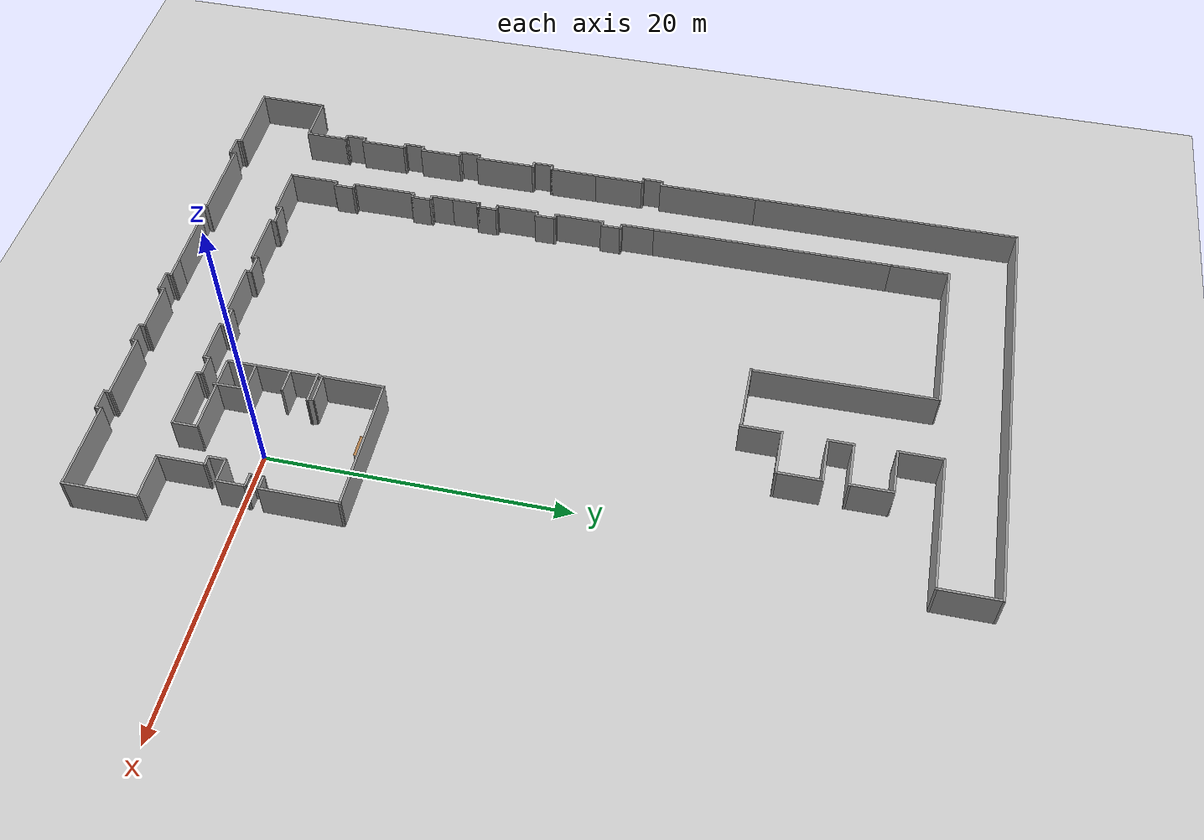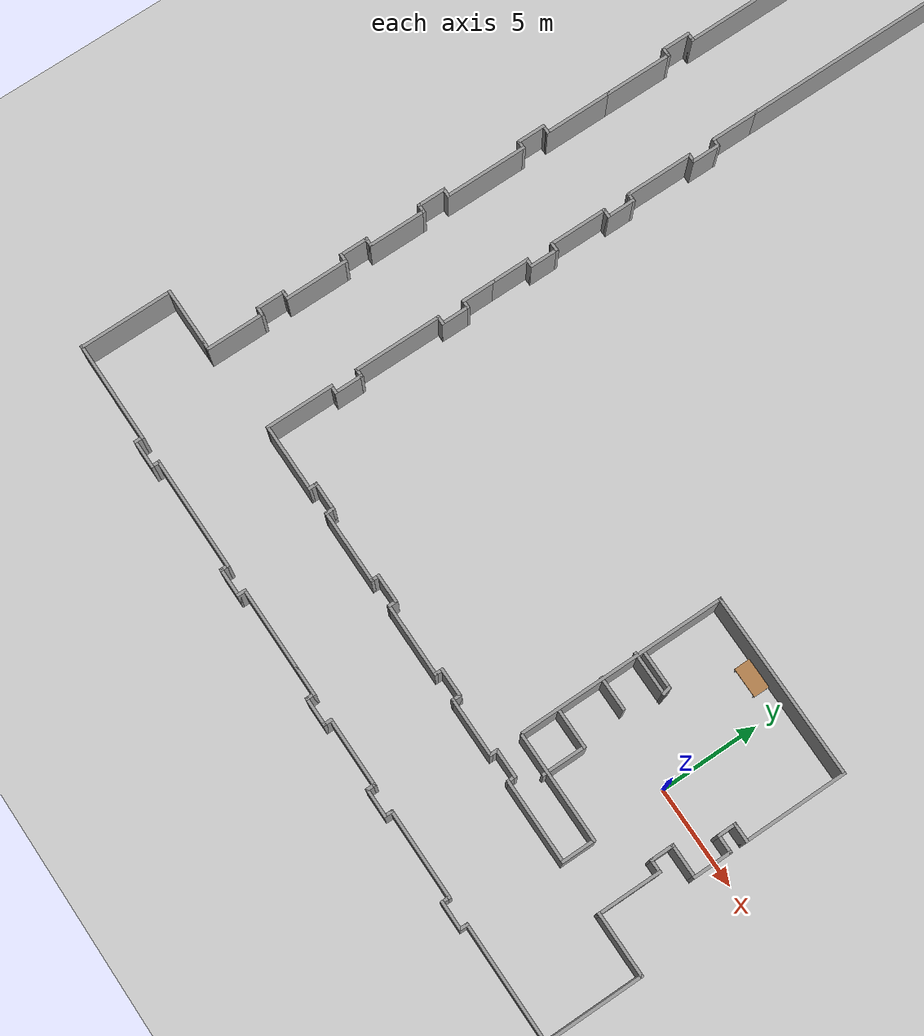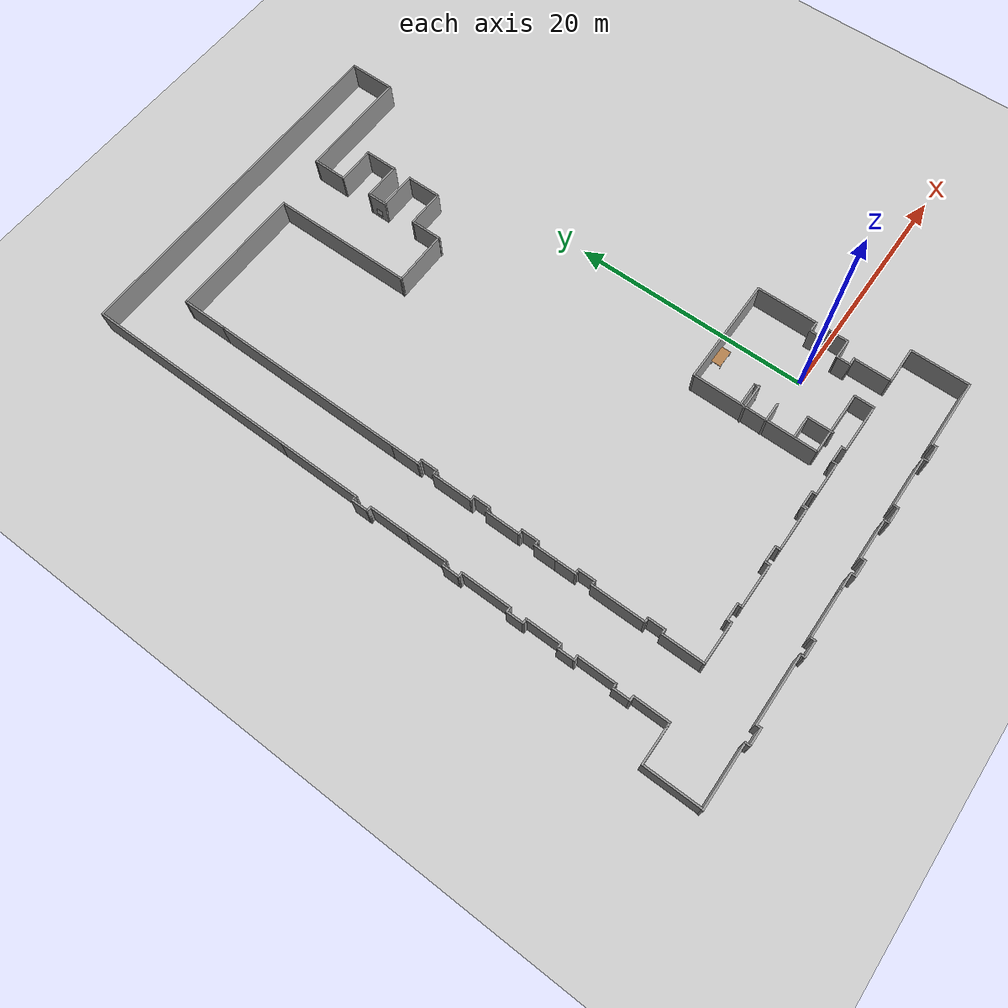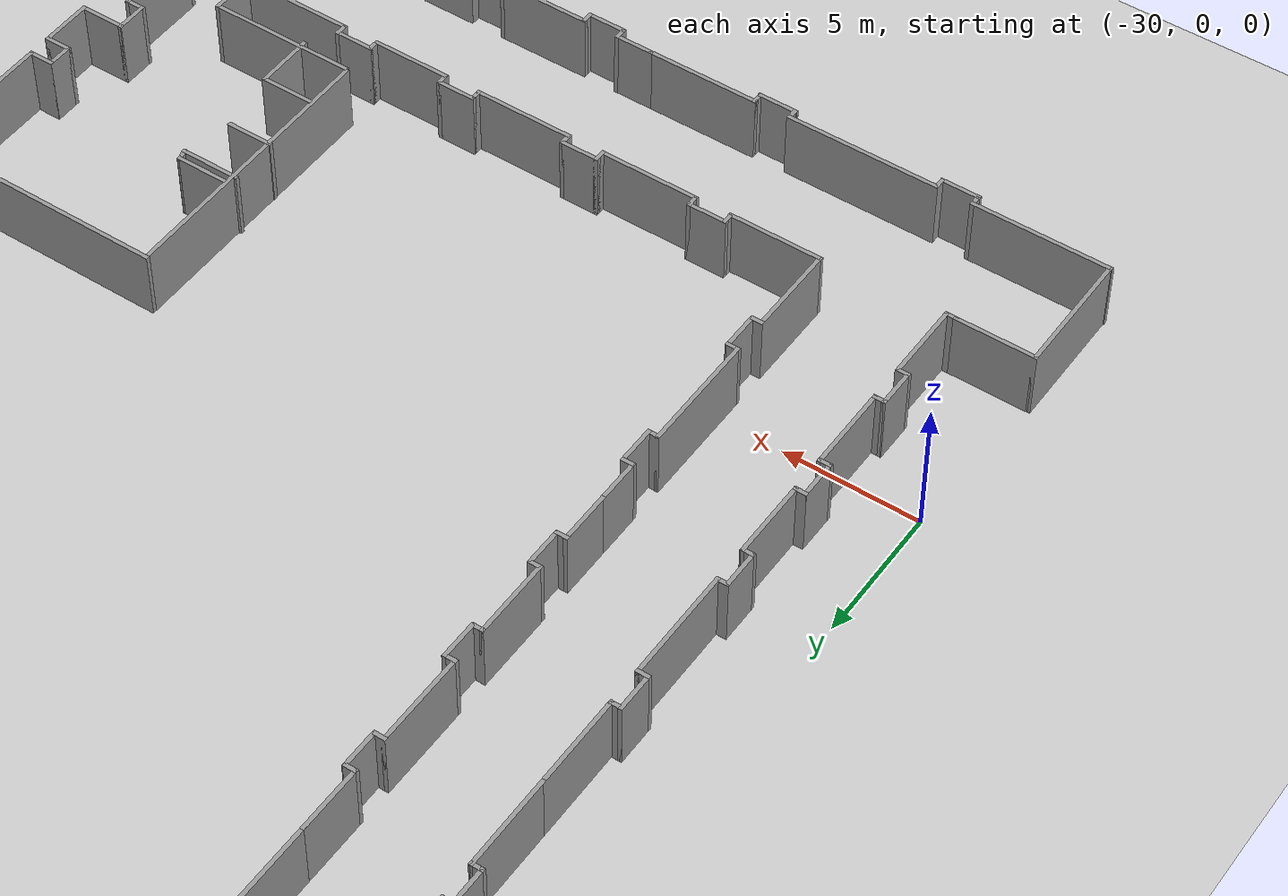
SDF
<sdf version="1.6">
 <world name="default">
  <light name="sun" type="directional">
   <pose>0 0 10 0 -0 0</pose>
   <diffuse>0.8 0.8 0.8 1</diffuse>
   <specular>0.2 0.2 0.2 1</specular>
   <attenuation>
    <range>1000</range>
    <constant>0.9</constant>
    <linear>0.01</linear>
    <quadratic>0.001</quadratic>
   </attenuation>
   <direction>-0.5 0.1 -0.9</direction>
  </light>
  <model name="ground_plane">
   <static>1</static>
   <link name="link">
    <collision name="collision">
     <geometry><plane><normal>0 0 1</normal><size>1 1</size></plane></geometry>
     <surface><friction><ode><mu>100</mu><mu2>50</mu2></ode></friction></surface>
    </collision>
    <visual name="visual">
     <cast_shadows>0</cast_shadows>
     <geometry><plane><normal>0 0 1</normal><size>1 1</size></plane></geometry>
     <material>
      <script><uri>file://media/materials/scripts/gazebo.material</uri><name>Gazebo/Grey</name></script>
     </material>
    </visual>
   </link>
  </model>
  <gravity>0 0 -9.8</gravity>
  <magnetic_field>6e-06 2.3e-05 -4.2e-05</magnetic_field>
  <atmosphere type="adiabatic"/>
  <physics name="default_physics" default="0" type="ode">
   <max_step_size>0.001</max_step_size>
   <real_time_factor>1</real_time_factor>
   <real_time_update_rate>1000</real_time_update_rate>
  </physics>
  <scene><ambient>0.4 0.4 0.4 1</ambient><background>0.7 0.7 0.7 1</background><shadows>1</shadows></scene>
  <audio><device>default</device></audio>
  <spherical_coordinates>
   <surface_model>EARTH_WGS84</surface_model>
   <latitude_deg>0</latitude_deg>
   <longitude_deg>0</longitude_deg>
   <elevation>0</elevation>
   <heading_deg>0</heading_deg>
  </spherical_coordinates>
  <model name="dstar_khu_5th_floor">
   <pose>-12.2572 17.3934 0 0 -0 0</pose>
   <link name="Wall_0">
    <collision name="Wall_0_Collision">
     <geometry><box><size>1.75 0.15 2.5</size></box></geometry>
     <pose>0 0 1.25 0 -0 0</pose>
    </collision>
    <visual name="Wall_0_Visual">
     <pose>0 0 1.25 0 -0 0</pose>
     <geometry><box><size>1.75 0.15 2.5</size></box></geometry>
     <material>
      <script><uri>file://media/materials/scripts/gazebo.material</uri><name>Gazebo/Grey</name></script>
      <ambient>1 1 1 1</ambient>
     </material>
     <meta><layer>0</layer></meta>
    </visual>
    <pose>12.4465 -22.1419 0 0 -0 1.5708</pose>
   </link>
   <link name="Wall_1">
    <collision name="Wall_1_Collision">
     <geometry><box><size>5.5 0.15 2.5</size></box></geometry>
     <pose>0 0 1.25 0 -0 0</pose>
    </collision>
    <visual name="Wall_1_Visual">
     <pose>0 0 1.25 0 -0 0</pose>
     <geometry><box><size>5.5 0.15 2.5</size></box></geometry>
     <material>
      <script><uri>file://media/materials/scripts/gazebo.material</uri><name>Gazebo/Grey</name></script>
      <ambient>1 1 1 1</ambient>
     </material>
     <meta><layer>0</layer></meta>
    </visual>
    <pose>9.77148 -21.3419 0 0 -0 3.14159</pose>
   </link>
   <link name="Wall_10">
    <collision name="Wall_10_Collision">
     <geometry><box><size>1 0.15 2.5</size></box></geometry>
     <pose>0 0 1.25 0 -0 0</pose>
    </collision>
    <visual name="Wall_10_Visual">
     <pose>0 0 1.25 0 -0 0</pose>
     <geometry><box><size>1 0.15 2.5</size></box></geometry>
     <material>
      <script><uri>file://media/materials/scripts/gazebo.material</uri><name>Gazebo/Grey</name></script>
      <ambient>1 1 1 1</ambient>
     </material>
     <meta><layer>0</layer></meta>
    </visual>
    <pose>15.6651 -16.8496 0 0 -0 3.14159</pose>
   </link>
   <link name="Wall_100">
    <collision name="Wall_100_Collision">
     <geometry><box><size>3.5 0.15 2.5</size></box></geometry>
     <pose>0 0 1.25 0 -0 0</pose>
    </collision>
    <visual name="Wall_100_Visual">
     <pose>0 0 1.25 0 -0 0</pose>
     <geometry><box><size>3.5 0.15 2.5</size></box></geometry>
     <material>
      <script><uri>file://media/materials/scripts/gazebo.material</uri><name>Gazebo/Grey</name></script>
      <ambient>1 1 1 1</ambient>
     </material>
     <meta><layer>0</layer></meta>
    </visual>
    <pose>-10.4535 -21.2669 0 0 -0 1.5708</pose>
   </link>
   <link name="Wall_101">
    <collision name="Wall_101_Collision">
     <geometry><box><size>0.5 0.15 2.5</size></box></geometry>
     <pose>0 0 1.25 0 -0 0</pose>
    </collision>
    <visual name="Wall_101_Visual">
     <pose>0 0 1.25 0 -0 0</pose>
     <geometry><box><size>0.5 0.15 2.5</size></box></geometry>
     <material>
      <script><uri>file://media/materials/scripts/gazebo.material</uri><name>Gazebo/Grey</name></script>
      <ambient>1 1 1 1</ambient>
     </material>
     <meta><layer>0</layer></meta>
    </visual>
    <pose>-10.2785 -19.5919 0 0 -0 0</pose>
   </link>
   <link name="Wall_104">
    <collision name="Wall_104_Collision">
     <geometry><box><size>1.5 0.15 2.5</size></box></geometry>
     <pose>0 0 1.25 0 -0 0</pose>
    </collision>
    <visual name="Wall_104_Visual">
     <pose>0 0 1.25 0 -0 0</pose>
     <geometry><box><size>1.5 0.15 2.5</size></box></geometry>
     <material>
      <script><uri>file://media/materials/scripts/gazebo.material</uri><name>Gazebo/Grey</name></script>
      <ambient>1 1 1 1</ambient>
     </material>
     <meta><layer>0</layer></meta>
    </visual>
    <pose>-10.1035 -18.9169 0 0 -0 1.5708</pose>
   </link>
   <link name="Wall_105">
    <collision name="Wall_105_Collision">
     <geometry><box><size>0.5 0.15 2.5</size></box></geometry>
     <pose>0 0 1.25 0 -0 0</pose>
    </collision>
    <visual name="Wall_105_Visual">
     <pose>0 0 1.25 0 -0 0</pose>
     <geometry><box><size>0.5 0.15 2.5</size></box></geometry>
     <material>
      <script><uri>file://media/materials/scripts/gazebo.material</uri><name>Gazebo/Grey</name></script>
      <ambient>1 1 1 1</ambient>
     </material>
     <meta><layer>0</layer></meta>
    </visual>
    <pose>-10.2785 -18.2419 0 0 -0 3.14159</pose>
   </link>
   <link name="Wall_108">
    <collision name="Wall_108_Collision">
     <geometry><box><size>4.5 0.15 2.5</size></box></geometry>
     <pose>0 0 1.25 0 -0 0</pose>
    </collision>
    <visual name="Wall_108_Visual">
     <pose>0 0 1.25 0 -0 0</pose>
     <geometry><box><size>4.5 0.15 2.5</size></box></geometry>
     <material>
      <script><uri>file://media/materials/scripts/gazebo.material</uri><name>Gazebo/Grey</name></script>
      <ambient>1 1 1 1</ambient>
     </material>
     <meta><layer>0</layer></meta>
    </visual>
    <pose>-10.4535 -16.0669 0 0 -0 1.5708</pose>
   </link>
   <link name="Wall_109">
    <collision name="Wall_109_Collision">
     <geometry><box><size>0.5 0.15 2.5</size></box></geometry>
     <pose>0 0 1.25 0 -0 0</pose>
    </collision>
    <visual name="Wall_109_Visual">
     <pose>0 0 1.25 0 -0 0</pose>
     <geometry><box><size>0.5 0.15 2.5</size></box></geometry>
     <material>
      <script><uri>file://media/materials/scripts/gazebo.material</uri><name>Gazebo/Grey</name></script>
      <ambient>1 1 1 1</ambient>
     </material>
     <meta><layer>0</layer></meta>
    </visual>
    <pose>-10.2785 -13.8919 0 0 -0 0</pose>
   </link>
   <link name="Wall_11">
    <collision name="Wall_11_Collision">
     <geometry><box><size>1 0.15 2.5</size></box></geometry>
     <pose>0 0 1.25 0 -0 0</pose>
    </collision>
    <visual name="Wall_11_Visual">
     <pose>0 0 1.25 0 -0 0</pose>
     <geometry><box><size>1 0.15 2.5</size></box></geometry>
     <material>
      <script><uri>file://media/materials/scripts/gazebo.material</uri><name>Gazebo/Grey</name></script>
      <ambient>1 1 1 1</ambient>
     </material>
     <meta><layer>0</layer></meta>
    </visual>
    <pose>15.2401 -16.4246 0 0 -0 1.5708</pose>
   </link>
   <link name="Wall_110">
    <collision name="Wall_110_Collision">
     <geometry><box><size>1.5 0.15 2.5</size></box></geometry>
     <pose>0 0 1.25 0 -0 0</pose>
    </collision>
    <visual name="Wall_110_Visual">
     <pose>0 0 1.25 0 -0 0</pose>
     <geometry><box><size>1.5 0.15 2.5</size></box></geometry>
     <material>
      <script><uri>file://media/materials/scripts/gazebo.material</uri><name>Gazebo/Grey</name></script>
      <ambient>1 1 1 1</ambient>
     </material>
     <meta><layer>0</layer></meta>
    </visual>
    <pose>-10.1035 -13.2169 0 0 -0 1.5708</pose>
   </link>
   <link name="Wall_111">
    <collision name="Wall_111_Collision">
     <geometry><box><size>0.5 0.15 2.5</size></box></geometry>
     <pose>0 0 1.25 0 -0 0</pose>
    </collision>
    <visual name="Wall_111_Visual">
     <pose>0 0 1.25 0 -0 0</pose>
     <geometry><box><size>0.5 0.15 2.5</size></box></geometry>
     <material>
      <script><uri>file://media/materials/scripts/gazebo.material</uri><name>Gazebo/Grey</name></script>
      <ambient>1 1 1 1</ambient>
     </material>
     <meta><layer>0</layer></meta>
    </visual>
    <pose>-10.2785 -12.5419 0 0 -0 3.14159</pose>
   </link>
   <link name="Wall_112">
    <collision name="Wall_112_Collision">
     <geometry><box><size>1.75 0.15 2.5</size></box></geometry>
     <pose>0 0 1.25 0 -0 0</pose>
    </collision>
    <visual name="Wall_112_Visual">
     <pose>0 0 1.25 0 -0 0</pose>
     <geometry><box><size>1.75 0.15 2.5</size></box></geometry>
     <material>
      <script><uri>file://media/materials/scripts/gazebo.material</uri><name>Gazebo/Grey</name></script>
      <ambient>1 1 1 1</ambient>
     </material>
     <meta><layer>0</layer></meta>
    </visual>
    <pose>-10.4535 -11.7419 0 0 -0 1.5708</pose>
   </link>
   <link name="Wall_114">
    <collision name="Wall_114_Collision">
     <geometry><box><size>2 0.15 2.5</size></box></geometry>
     <pose>0 0 1.25 0 -0 0</pose>
    </collision>
    <visual name="Wall_114_Visual">
     <pose>0 0 1.25 0 -0 0</pose>
     <geometry><box><size>2 0.15 2.5</size></box></geometry>
     <material>
      <script><uri>file://media/materials/scripts/gazebo.material</uri><name>Gazebo/Grey</name></script>
      <ambient>1 1 1 1</ambient>
     </material>
     <meta><layer>0</layer></meta>
    </visual>
    <pose>-10.4535 -10.0169 0 0 -0 1.5708</pose>
   </link>
   <link name="Wall_115">
    <collision name="Wall_115_Collision">
     <geometry><box><size>0.5 0.15 2.5</size></box></geometry>
     <pose>0 0 1.25 0 -0 0</pose>
    </collision>
    <visual name="Wall_115_Visual">
     <pose>0 0 1.25 0 -0 0</pose>
     <geometry><box><size>0.5 0.15 2.5</size></box></geometry>
     <material>
      <script><uri>file://media/materials/scripts/gazebo.material</uri><name>Gazebo/Grey</name></script>
      <ambient>1 1 1 1</ambient>
     </material>
     <meta><layer>0</layer></meta>
    </visual>
    <pose>-10.2785 -9.09191 0 0 -0 0</pose>
   </link>
   <link name="Wall_116">
    <collision name="Wall_116_Collision">
     <geometry><box><size>1.5 0.15 2.5</size></box></geometry>
     <pose>0 0 1.25 0 -0 0</pose>
    </collision>
    <visual name="Wall_116_Visual">
     <pose>0 0 1.25 0 -0 0</pose>
     <geometry><box><size>1.5 0.15 2.5</size></box></geometry>
     <material>
      <script><uri>file://media/materials/scripts/gazebo.material</uri><name>Gazebo/Grey</name></script>
      <ambient>1 1 1 1</ambient>
     </material>
     <meta><layer>0</layer></meta>
    </visual>
    <pose>-10.1035 -8.41691 0 0 -0 1.5708</pose>
   </link>
   <link name="Wall_117">
    <collision name="Wall_117_Collision">
     <geometry><box><size>0.5 0.15 2.5</size></box></geometry>
     <pose>0 0 1.25 0 -0 0</pose>
    </collision>
    <visual name="Wall_117_Visual">
     <pose>0 0 1.25 0 -0 0</pose>
     <geometry><box><size>0.5 0.15 2.5</size></box></geometry>
     <material>
      <script><uri>file://media/materials/scripts/gazebo.material</uri><name>Gazebo/Grey</name></script>
      <ambient>1 1 1 1</ambient>
     </material>
     <meta><layer>0</layer></meta>
    </visual>
    <pose>-10.2785 -7.74191 0 0 -0 3.14159</pose>
   </link>
   <link name="Wall_118">
    <collision name="Wall_118_Collision">
     <geometry><box><size>3 0.15 2.5</size></box></geometry>
     <pose>0 0 1.25 0 -0 0</pose>
    </collision>
    <visual name="Wall_118_Visual">
     <pose>0 0 1.25 0 -0 0</pose>
     <geometry><box><size>3 0.15 2.5</size></box></geometry>
     <material>
      <script><uri>file://media/materials/scripts/gazebo.material</uri><name>Gazebo/Grey</name></script>
      <ambient>1 1 1 1</ambient>
     </material>
     <meta><layer>0</layer></meta>
    </visual>
    <pose>-10.4535 -6.31691 0 0 -0 1.5708</pose>
   </link>
   <link name="Wall_12">
    <collision name="Wall_12_Collision">
     <geometry><box><size>1 0.15 2.5</size></box></geometry>
     <pose>0 0 1.25 0 -0 0</pose>
    </collision>
    <visual name="Wall_12_Visual">
     <pose>0 0 1.25 0 -0 0</pose>
     <geometry><box><size>1 0.15 2.5</size></box></geometry>
     <material>
      <script><uri>file://media/materials/scripts/gazebo.material</uri><name>Gazebo/Grey</name></script>
      <ambient>1 1 1 1</ambient>
     </material>
     <meta><layer>0</layer></meta>
    </visual>
    <pose>15.6651 -15.9996 0 0 -0 0</pose>
   </link>
   <link name="Wall_121">
    <collision name="Wall_121_Collision">
     <geometry><box><size>0.5 0.15 2.5</size></box></geometry>
     <pose>0 0 1.25 0 -0 0</pose>
    </collision>
    <visual name="Wall_121_Visual">
     <pose>0 0 1.25 0 -0 0</pose>
     <geometry><box><size>0.5 0.15 2.5</size></box></geometry>
     <material>
      <script><uri>file://media/materials/scripts/gazebo.material</uri><name>Gazebo/Grey</name></script>
      <ambient>1 1 1 1</ambient>
     </material>
     <meta><layer>0</layer></meta>
    </visual>
    <pose>-10.2785 -4.89191 0 0 -0 0</pose>
   </link>
   <link name="Wall_122">
    <collision name="Wall_122_Collision">
     <geometry><box><size>1.5 0.15 2.5</size></box></geometry>
     <pose>0 0 1.25 0 -0 0</pose>
    </collision>
    <visual name="Wall_122_Visual">
     <pose>0 0 1.25 0 -0 0</pose>
     <geometry><box><size>1.5 0.15 2.5</size></box></geometry>
     <material>
      <script><uri>file://media/materials/scripts/gazebo.material</uri><name>Gazebo/Grey</name></script>
      <ambient>1 1 1 1</ambient>
     </material>
     <meta><layer>0</layer></meta>
    </visual>
    <pose>-10.1035 -4.21691 0 0 -0 1.5708</pose>
   </link>
   <link name="Wall_123">
    <collision name="Wall_123_Collision">
     <geometry><box><size>0.5 0.15 2.5</size></box></geometry>
     <pose>0 0 1.25 0 -0 0</pose>
    </collision>
    <visual name="Wall_123_Visual">
     <pose>0 0 1.25 0 -0 0</pose>
     <geometry><box><size>0.5 0.15 2.5</size></box></geometry>
     <material>
      <script><uri>file://media/materials/scripts/gazebo.material</uri><name>Gazebo/Grey</name></script>
      <ambient>1 1 1 1</ambient>
     </material>
     <meta><layer>0</layer></meta>
    </visual>
    <pose>-10.2785 -3.54191 0 0 -0 3.14159</pose>
   </link>
   <link name="Wall_124">
    <collision name="Wall_124_Collision">
     <geometry><box><size>3.5 0.15 2.5</size></box></geometry>
     <pose>0 0 1.25 0 -0 0</pose>
    </collision>
    <visual name="Wall_124_Visual">
     <pose>0 0 1.25 0 -0 0</pose>
     <geometry><box><size>3.5 0.15 2.5</size></box></geometry>
     <material>
      <script><uri>file://media/materials/scripts/gazebo.material</uri><name>Gazebo/Grey</name></script>
      <ambient>1 1 1 1</ambient>
     </material>
     <meta><layer>0</layer></meta>
    </visual>
    <pose>-10.4535 -1.86691 0 0 -0 1.5708</pose>
   </link>
   <link name="Wall_127">
    <collision name="Wall_127_Collision">
     <geometry><box><size>0.5 0.15 2.5</size></box></geometry>
     <pose>0 0 1.25 0 -0 0</pose>
    </collision>
    <visual name="Wall_127_Visual">
     <pose>0 0 1.25 0 -0 0</pose>
     <geometry><box><size>0.5 0.15 2.5</size></box></geometry>
     <material>
      <script><uri>file://media/materials/scripts/gazebo.material</uri><name>Gazebo/Grey</name></script>
      <ambient>1 1 1 1</ambient>
     </material>
     <meta><layer>0</layer></meta>
    </visual>
    <pose>-10.2785 -0.191909 0 0 -0 0</pose>
   </link>
   <link name="Wall_128">
    <collision name="Wall_128_Collision">
     <geometry><box><size>1.5 0.15 2.5</size></box></geometry>
     <pose>0 0 1.25 0 -0 0</pose>
    </collision>
    <visual name="Wall_128_Visual">
     <pose>0 0 1.25 0 -0 0</pose>
     <geometry><box><size>1.5 0.15 2.5</size></box></geometry>
     <material>
      <script><uri>file://media/materials/scripts/gazebo.material</uri><name>Gazebo/Grey</name></script>
      <ambient>1 1 1 1</ambient>
     </material>
     <meta><layer>0</layer></meta>
    </visual>
    <pose>-10.1035 0.483091 0 0 -0 1.5708</pose>
   </link>
   <link name="Wall_129">
    <collision name="Wall_129_Collision">
     <geometry><box><size>0.5 0.15 2.5</size></box></geometry>
     <pose>0 0 1.25 0 -0 0</pose>
    </collision>
    <visual name="Wall_129_Visual">
     <pose>0 0 1.25 0 -0 0</pose>
     <geometry><box><size>0.5 0.15 2.5</size></box></geometry>
     <material>
      <script><uri>file://media/materials/scripts/gazebo.material</uri><name>Gazebo/Grey</name></script>
      <ambient>1 1 1 1</ambient>
     </material>
     <meta><layer>0</layer></meta>
    </visual>
    <pose>-10.2785 1.15809 0 0 -0 3.14159</pose>
   </link>
   <link name="Wall_13">
    <collision name="Wall_13_Collision">
     <geometry><box><size>5.25 0.15 2.5</size></box></geometry>
     <pose>0 0 1.25 0 -0 0</pose>
    </collision>
    <visual name="Wall_13_Visual">
     <pose>0 0 1.25 0 -0 0</pose>
     <geometry><box><size>5.25 0.15 2.5</size></box></geometry>
     <material>
      <script><uri>file://media/materials/scripts/gazebo.material</uri><name>Gazebo/Grey</name></script>
      <ambient>1 1 1 1</ambient>
     </material>
     <meta><layer>0</layer></meta>
    </visual>
    <pose>16.0901 -13.4496 0 0 -0 1.5708</pose>
   </link>
   <link name="Wall_130">
    <collision name="Wall_130_Collision">
     <geometry><box><size>2.5 0.15 2.5</size></box></geometry>
     <pose>0 0 1.25 0 -0 0</pose>
    </collision>
    <visual name="Wall_130_Visual">
     <pose>0 0 1.25 0 -0 0</pose>
     <geometry><box><size>2.5 0.15 2.5</size></box></geometry>
     <material>
      <script><uri>file://media/materials/scripts/gazebo.material</uri><name>Gazebo/Grey</name></script>
      <ambient>1 1 1 1</ambient>
     </material>
     <meta><layer>0</layer></meta>
    </visual>
    <pose>-10.4535 2.33309 0 0 -0 1.5708</pose>
   </link>
   <link name="Wall_132">
    <collision name="Wall_132_Collision">
     <geometry><box><size>0.5 0.15 2.5</size></box></geometry>
     <pose>0 0 1.25 0 -0 0</pose>
    </collision>
    <visual name="Wall_132_Visual">
     <pose>0 0 1.25 0 -0 0</pose>
     <geometry><box><size>0.5 0.15 2.5</size></box></geometry>
     <material>
      <script><uri>file://media/materials/scripts/gazebo.material</uri><name>Gazebo/Grey</name></script>
      <ambient>1 1 1 1</ambient>
     </material>
     <meta><layer>0</layer></meta>
    </visual>
    <pose>-15.1361 -18.975 0 0 -0 0</pose>
   </link>
   <link name="Wall_133">
    <collision name="Wall_133_Collision">
     <geometry><box><size>3.25 0.15 2.5</size></box></geometry>
     <pose>0 0 1.25 0 -0 0</pose>
    </collision>
    <visual name="Wall_133_Visual">
     <pose>0 0 1.25 0 -0 0</pose>
     <geometry><box><size>3.25 0.15 2.5</size></box></geometry>
     <material>
      <script><uri>file://media/materials/scripts/gazebo.material</uri><name>Gazebo/Grey</name></script>
      <ambient>1 1 1 1</ambient>
     </material>
     <meta><layer>0</layer></meta>
    </visual>
    <pose>-14.9611 -17.425 0 0 -0 1.5708</pose>
   </link>
   <link name="Wall_134">
    <collision name="Wall_134_Collision">
     <geometry><box><size>0.5 0.15 2.5</size></box></geometry>
     <pose>0 0 1.25 0 -0 0</pose>
    </collision>
    <visual name="Wall_134_Visual">
     <pose>0 0 1.25 0 -0 0</pose>
     <geometry><box><size>0.5 0.15 2.5</size></box></geometry>
     <material>
      <script><uri>file://media/materials/scripts/gazebo.material</uri><name>Gazebo/Grey</name></script>
      <ambient>1 1 1 1</ambient>
     </material>
     <meta><layer>0</layer></meta>
    </visual>
    <pose>-15.1361 -15.875 0 0 -0 3.14159</pose>
   </link>
   <link name="Wall_135">
    <collision name="Wall_135_Collision">
     <geometry><box><size>1.5 0.15 2.5</size></box></geometry>
     <pose>0 0 1.25 0 -0 0</pose>
    </collision>
    <visual name="Wall_135_Visual">
     <pose>0 0 1.25 0 -0 0</pose>
     <geometry><box><size>1.5 0.15 2.5</size></box></geometry>
     <material>
      <script><uri>file://media/materials/scripts/gazebo.material</uri><name>Gazebo/Grey</name></script>
      <ambient>1 1 1 1</ambient>
     </material>
     <meta><layer>0</layer></meta>
    </visual>
    <pose>-15.3111 -15.2 0 0 -0 1.5708</pose>
   </link>
   <link name="Wall_136">
    <collision name="Wall_136_Collision">
     <geometry><box><size>0.5 0.15 2.5</size></box></geometry>
     <pose>0 0 1.25 0 -0 0</pose>
    </collision>
    <visual name="Wall_136_Visual">
     <pose>0 0 1.25 0 -0 0</pose>
     <geometry><box><size>0.5 0.15 2.5</size></box></geometry>
     <material>
      <script><uri>file://media/materials/scripts/gazebo.material</uri><name>Gazebo/Grey</name></script>
      <ambient>1 1 1 1</ambient>
     </material>
     <meta><layer>0</layer></meta>
    </visual>
    <pose>-15.1361 -14.525 0 0 -0 0</pose>
   </link>
   <link name="Wall_137">
    <collision name="Wall_137_Collision">
     <geometry><box><size>3 0.15 2.5</size></box></geometry>
     <pose>0 0 1.25 0 -0 0</pose>
    </collision>
    <visual name="Wall_137_Visual">
     <pose>0 0 1.25 0 -0 0</pose>
     <geometry><box><size>3 0.15 2.5</size></box></geometry>
     <material>
      <script><uri>file://media/materials/scripts/gazebo.material</uri><name>Gazebo/Grey</name></script>
      <ambient>1 1 1 1</ambient>
     </material>
     <meta><layer>0</layer></meta>
    </visual>
    <pose>-14.9611 -13.1 0 0 -0 1.5708</pose>
   </link>
   <link name="Wall_140">
    <collision name="Wall_140_Collision">
     <geometry><box><size>0.5 0.15 2.5</size></box></geometry>
     <pose>0 0 1.25 0 -0 0</pose>
    </collision>
    <visual name="Wall_140_Visual">
     <pose>0 0 1.25 0 -0 0</pose>
     <geometry><box><size>0.5 0.15 2.5</size></box></geometry>
     <material>
      <script><uri>file://media/materials/scripts/gazebo.material</uri><name>Gazebo/Grey</name></script>
      <ambient>1 1 1 1</ambient>
     </material>
     <meta><layer>0</layer></meta>
    </visual>
    <pose>-15.1361 -11.675 0 0 -0 3.14159</pose>
   </link>
   <link name="Wall_141">
    <collision name="Wall_141_Collision">
     <geometry><box><size>1.5 0.15 2.5</size></box></geometry>
     <pose>0 0 1.25 0 -0 0</pose>
    </collision>
    <visual name="Wall_141_Visual">
     <pose>0 0 1.25 0 -0 0</pose>
     <geometry><box><size>1.5 0.15 2.5</size></box></geometry>
     <material>
      <script><uri>file://media/materials/scripts/gazebo.material</uri><name>Gazebo/Grey</name></script>
      <ambient>1 1 1 1</ambient>
     </material>
     <meta><layer>0</layer></meta>
    </visual>
    <pose>-15.3111 -11 0 0 -0 1.5708</pose>
   </link>
   <link name="Wall_142">
    <collision name="Wall_142_Collision">
     <geometry><box><size>0.5 0.15 2.5</size></box></geometry>
     <pose>0 0 1.25 0 -0 0</pose>
    </collision>
    <visual name="Wall_142_Visual">
     <pose>0 0 1.25 0 -0 0</pose>
     <geometry><box><size>0.5 0.15 2.5</size></box></geometry>
     <material>
      <script><uri>file://media/materials/scripts/gazebo.material</uri><name>Gazebo/Grey</name></script>
      <ambient>1 1 1 1</ambient>
     </material>
     <meta><layer>0</layer></meta>
    </visual>
    <pose>-15.1361 -10.325 0 0 -0 0</pose>
   </link>
   <link name="Wall_143">
    <collision name="Wall_143_Collision">
     <geometry><box><size>4.25 0.15 2.5</size></box></geometry>
     <pose>0 0 1.25 0 -0 0</pose>
    </collision>
    <visual name="Wall_143_Visual">
     <pose>0 0 1.25 0 -0 0</pose>
     <geometry><box><size>4.25 0.15 2.5</size></box></geometry>
     <material>
      <script><uri>file://media/materials/scripts/gazebo.material</uri><name>Gazebo/Grey</name></script>
      <ambient>1 1 1 1</ambient>
     </material>
     <meta><layer>0</layer></meta>
    </visual>
    <pose>-14.9611 -8.275 0 0 -0 1.5708</pose>
   </link>
   <link name="Wall_145">
    <collision name="Wall_145_Collision">
     <geometry><box><size>0.5 0.15 2.5</size></box></geometry>
     <pose>0 0 1.25 0 -0 0</pose>
    </collision>
    <visual name="Wall_145_Visual">
     <pose>0 0 1.25 0 -0 0</pose>
     <geometry><box><size>0.5 0.15 2.5</size></box></geometry>
     <material>
      <script><uri>file://media/materials/scripts/gazebo.material</uri><name>Gazebo/Grey</name></script>
      <ambient>1 1 1 1</ambient>
     </material>
     <meta><layer>0</layer></meta>
    </visual>
    <pose>-15.1361 -6.225 0 0 -0 3.14159</pose>
   </link>
   <link name="Wall_146">
    <collision name="Wall_146_Collision">
     <geometry><box><size>1.5 0.15 2.5</size></box></geometry>
     <pose>0 0 1.25 0 -0 0</pose>
    </collision>
    <visual name="Wall_146_Visual">
     <pose>0 0 1.25 0 -0 0</pose>
     <geometry><box><size>1.5 0.15 2.5</size></box></geometry>
     <material>
      <script><uri>file://media/materials/scripts/gazebo.material</uri><name>Gazebo/Grey</name></script>
      <ambient>1 1 1 1</ambient>
     </material>
     <meta><layer>0</layer></meta>
    </visual>
    <pose>-15.3111 -5.55 0 0 -0 1.5708</pose>
   </link>
   <link name="Wall_147">
    <collision name="Wall_147_Collision">
     <geometry><box><size>0.5 0.15 2.5</size></box></geometry>
     <pose>0 0 1.25 0 -0 0</pose>
    </collision>
    <visual name="Wall_147_Visual">
     <pose>0 0 1.25 0 -0 0</pose>
     <geometry><box><size>0.5 0.15 2.5</size></box></geometry>
     <material>
      <script><uri>file://media/materials/scripts/gazebo.material</uri><name>Gazebo/Grey</name></script>
      <ambient>1 1 1 1</ambient>
     </material>
     <meta><layer>0</layer></meta>
    </visual>
    <pose>-15.1361 -4.875 0 0 -0 0</pose>
   </link>
   <link name="Wall_148">
    <collision name="Wall_148_Collision">
     <geometry><box><size>3.5 0.15 2.5</size></box></geometry>
     <pose>0 0 1.25 0 -0 0</pose>
    </collision>
    <visual name="Wall_148_Visual">
     <pose>0 0 1.25 0 -0 0</pose>
     <geometry><box><size>3.5 0.15 2.5</size></box></geometry>
     <material>
      <script><uri>file://media/materials/scripts/gazebo.material</uri><name>Gazebo/Grey</name></script>
      <ambient>1 1 1 1</ambient>
     </material>
     <meta><layer>0</layer></meta>
    </visual>
    <pose>-14.9611 -3.2 0 0 -0 1.5708</pose>
   </link>
   <link name="Wall_150">
    <collision name="Wall_150_Collision">
     <geometry><box><size>3.5 0.15 2.5</size></box></geometry>
     <pose>0 0 1.25 0 -0 0</pose>
    </collision>
    <visual name="Wall_150_Visual">
     <pose>0 0 1.25 0 -0 0</pose>
     <geometry><box><size>3.5 0.15 2.5</size></box></geometry>
     <material>
      <script><uri>file://media/materials/scripts/gazebo.material</uri><name>Gazebo/Grey</name></script>
      <ambient>1 1 1 1</ambient>
     </material>
     <meta><layer>0</layer></meta>
    </visual>
    <pose>-14.9611 0.149999 0 0 -0 1.5708</pose>
   </link>
   <link name="Wall_152">
    <collision name="Wall_152_Collision">
     <geometry><box><size>0.5 0.15 2.5</size></box></geometry>
     <pose>0 0 1.25 0 -0 0</pose>
    </collision>
    <visual name="Wall_152_Visual">
     <pose>0 0 1.25 0 -0 0</pose>
     <geometry><box><size>0.5 0.15 2.5</size></box></geometry>
     <material>
      <script><uri>file://media/materials/scripts/gazebo.material</uri><name>Gazebo/Grey</name></script>
      <ambient>1 1 1 1</ambient>
     </material>
     <meta><layer>0</layer></meta>
    </visual>
    <pose>-15.1361 1.825 0 0 -0 3.14159</pose>
   </link>
   <link name="Wall_153">
    <collision name="Wall_153_Collision">
     <geometry><box><size>1.5 0.15 2.5</size></box></geometry>
     <pose>0 0 1.25 0 -0 0</pose>
    </collision>
    <visual name="Wall_153_Visual">
     <pose>0 0 1.25 0 -0 0</pose>
     <geometry><box><size>1.5 0.15 2.5</size></box></geometry>
     <material>
      <script><uri>file://media/materials/scripts/gazebo.material</uri><name>Gazebo/Grey</name></script>
      <ambient>1 1 1 1</ambient>
     </material>
     <meta><layer>0</layer></meta>
    </visual>
    <pose>-15.3111 2.5 0 0 -0 1.5708</pose>
   </link>
   <link name="Wall_154">
    <collision name="Wall_154_Collision">
     <geometry><box><size>0.5 0.15 2.5</size></box></geometry>
     <pose>0 0 1.25 0 -0 0</pose>
    </collision>
    <visual name="Wall_154_Visual">
     <pose>0 0 1.25 0 -0 0</pose>
     <geometry><box><size>0.5 0.15 2.5</size></box></geometry>
     <material>
      <script><uri>file://media/materials/scripts/gazebo.material</uri><name>Gazebo/Grey</name></script>
      <ambient>1 1 1 1</ambient>
     </material>
     <meta><layer>0</layer></meta>
    </visual>
    <pose>-15.1361 3.175 0 0 -0 0</pose>
   </link>
   <link name="Wall_155">
    <collision name="Wall_155_Collision">
     <geometry><box><size>7 0.15 2.5</size></box></geometry>
     <pose>0 0 1.25 0 -0 0</pose>
    </collision>
    <visual name="Wall_155_Visual">
     <pose>0 0 1.25 0 -0 0</pose>
     <geometry><box><size>7 0.15 2.5</size></box></geometry>
     <material>
      <script><uri>file://media/materials/scripts/gazebo.material</uri><name>Gazebo/Grey</name></script>
      <ambient>1 1 1 1</ambient>
     </material>
     <meta><layer>0</layer></meta>
    </visual>
    <pose>-14.9611 6.6 0 0 -0 1.5708</pose>
   </link>
   <link name="Wall_157">
    <collision name="Wall_157_Collision">
     <geometry><box><size>16.5 0.15 2.5</size></box></geometry>
     <pose>0 0 1.25 0 -0 0</pose>
    </collision>
    <visual name="Wall_157_Visual">
     <pose>0 0 1.25 0 -0 0</pose>
     <geometry><box><size>16.5 0.15 2.5</size></box></geometry>
     <material>
      <script><uri>file://media/materials/scripts/gazebo.material</uri><name>Gazebo/Grey</name></script>
      <ambient>1 1 1 1</ambient>
     </material>
     <meta><layer>0</layer></meta>
    </visual>
    <pose>-10.4535 11.6831 0 0 -0 1.5708</pose>
   </link>
   <link name="Wall_159">
    <collision name="Wall_159_Collision">
     <geometry><box><size>18.25 0.15 2.5</size></box></geometry>
     <pose>0 0 1.25 0 -0 0</pose>
    </collision>
    <visual name="Wall_159_Visual">
     <pose>0 0 1.25 0 -0 0</pose>
     <geometry><box><size>18.25 0.15 2.5</size></box></geometry>
     <material>
      <script><uri>file://media/materials/scripts/gazebo.material</uri><name>Gazebo/Grey</name></script>
      <ambient>1 1 1 1</ambient>
     </material>
     <meta><layer>0</layer></meta>
    </visual>
    <pose>-14.9611 19.075 0 0 -0 1.5708</pose>
   </link>
   <link name="Wall_161">
    <collision name="Wall_161_Collision">
     <geometry><box><size>4 0.15 2.5</size></box></geometry>
     <pose>0 0 1.25 0 -0 0</pose>
    </collision>
    <visual name="Wall_161_Visual">
     <pose>0 0 1.25 0 -0 0</pose>
     <geometry><box><size>4 0.15 2.5</size></box></geometry>
     <material>
      <script><uri>file://media/materials/scripts/gazebo.material</uri><name>Gazebo/Grey</name></script>
      <ambient>1 1 1 1</ambient>
     </material>
     <meta><layer>0</layer></meta>
    </visual>
    <pose>-10.4535 21.7831 0 0 -0 1.5708</pose>
   </link>
   <link name="Wall_162">
    <collision name="Wall_162_Collision">
     <geometry><box><size>11.25 0.15 2.5</size></box></geometry>
     <pose>0 0 1.25 0 -0 0</pose>
    </collision>
    <visual name="Wall_162_Visual">
     <pose>0 0 1.25 0 -0 0</pose>
     <geometry><box><size>11.25 0.15 2.5</size></box></geometry>
     <material>
      <script><uri>file://media/materials/scripts/gazebo.material</uri><name>Gazebo/Grey</name></script>
      <ambient>1 1 1 1</ambient>
     </material>
     <meta><layer>0</layer></meta>
    </visual>
    <pose>-4.90352 23.7081 0 0 -0 0</pose>
   </link>
   <link name="Wall_163">
    <collision name="Wall_163_Collision">
     <geometry><box><size>12.1255 0.15 2.5</size></box></geometry>
     <pose>0 0 1.25 0 -0 0</pose>
    </collision>
    <visual name="Wall_163_Visual">
     <pose>0 0 1.25 0 -0 0</pose>
     <geometry><box><size>12.1255 0.15 2.5</size></box></geometry>
     <material>
      <script><uri>file://media/materials/scripts/gazebo.material</uri><name>Gazebo/Grey</name></script>
      <ambient>1 1 1 1</ambient>
     </material>
     <meta><layer>0</layer></meta>
    </visual>
    <pose>0.684281 17.7204 0 0 -0 -1.56448</pose>
   </link>
   <link name="Wall_164">
    <collision name="Wall_164_Collision">
     <geometry><box><size>4.75 0.15 2.5</size></box></geometry>
     <pose>0 0 1.25 0 -0 0</pose>
    </collision>
    <visual name="Wall_164_Visual">
     <pose>0 0 1.25 0 -0 0</pose>
     <geometry><box><size>4.75 0.15 2.5</size></box></geometry>
     <material>
      <script><uri>file://media/materials/scripts/gazebo.material</uri><name>Gazebo/Grey</name></script>
      <ambient>1 1 1 1</ambient>
     </material>
     <meta><layer>0</layer></meta>
    </visual>
    <pose>2.98428 11.7328 0 0 -0 0</pose>
   </link>
   <link name="Wall_166">
    <collision name="Wall_166_Collision">
     <geometry><box><size>29.75 0.15 2.5</size></box></geometry>
     <pose>0 0 1.25 0 -0 0</pose>
    </collision>
    <visual name="Wall_166_Visual">
     <pose>0 0 1.25 0 -0 0</pose>
     <geometry><box><size>29.75 0.15 2.5</size></box></geometry>
     <material>
      <script><uri>file://media/materials/scripts/gazebo.material</uri><name>Gazebo/Grey</name></script>
      <ambient>1 1 1 1</ambient>
     </material>
     <meta><layer>0</layer></meta>
    </visual>
    <pose>-0.161055 28.125 0 0 -0 0</pose>
   </link>
   <link name="Wall_168">
    <collision name="Wall_168_Collision">
     <geometry><box><size>4 0.15 2.5</size></box></geometry>
     <pose>0 0 1.25 0 -0 0</pose>
    </collision>
    <visual name="Wall_168_Visual">
     <pose>0 0 1.25 0 -0 0</pose>
     <geometry><box><size>4 0.15 2.5</size></box></geometry>
     <material>
      <script><uri>file://media/materials/scripts/gazebo.material</uri><name>Gazebo/Grey</name></script>
      <ambient>1 1 1 1</ambient>
     </material>
     <meta><layer>0</layer></meta>
    </visual>
    <pose>14.6389 26.2 0 0 -0 -1.5708</pose>
   </link>
   <link name="Wall_169">
    <collision name="Wall_169_Collision">
     <geometry><box><size>9.5 0.15 2.5</size></box></geometry>
     <pose>0 0 1.25 0 -0 0</pose>
    </collision>
    <visual name="Wall_169_Visual">
     <pose>0 0 1.25 0 -0 0</pose>
     <geometry><box><size>9.5 0.15 2.5</size></box></geometry>
     <material>
      <script><uri>file://media/materials/scripts/gazebo.material</uri><name>Gazebo/Grey</name></script>
      <ambient>1 1 1 1</ambient>
     </material>
     <meta><layer>0</layer></meta>
    </visual>
    <pose>9.96395 24.275 0 0 -0 3.14159</pose>
   </link>
   <link name="Wall_170">
    <collision name="Wall_170_Collision">
     <geometry><box><size>3 0.15 2.5</size></box></geometry>
     <pose>0 0 1.25 0 -0 0</pose>
    </collision>
    <visual name="Wall_170_Visual">
     <pose>0 0 1.25 0 -0 0</pose>
     <geometry><box><size>3 0.15 2.5</size></box></geometry>
     <material>
      <script><uri>file://media/materials/scripts/gazebo.material</uri><name>Gazebo/Grey</name></script>
      <ambient>1 1 1 1</ambient>
     </material>
     <meta><layer>0</layer></meta>
    </visual>
    <pose>5.28895 22.85 0 0 -0 -1.5708</pose>
   </link>
   <link name="Wall_171">
    <collision name="Wall_171_Collision">
     <geometry><box><size>3.25 0.15 2.5</size></box></geometry>
     <pose>0 0 1.25 0 -0 0</pose>
    </collision>
    <visual name="Wall_171_Visual">
     <pose>0 0 1.25 0 -0 0</pose>
     <geometry><box><size>3.25 0.15 2.5</size></box></geometry>
     <material>
      <script><uri>file://media/materials/scripts/gazebo.material</uri><name>Gazebo/Grey</name></script>
      <ambient>1 1 1 1</ambient>
     </material>
     <meta><layer>0</layer></meta>
    </visual>
    <pose>6.83894 21.425 0 0 -0 0</pose>
   </link>
   <link name="Wall_172">
    <collision name="Wall_172_Collision">
     <geometry><box><size>2.83014 0.15 2.5</size></box></geometry>
     <pose>0 0 1.25 0 -0 0</pose>
    </collision>
    <visual name="Wall_172_Visual">
     <pose>0 0 1.25 0 -0 0</pose>
     <geometry><box><size>2.83014 0.15 2.5</size></box></geometry>
     <material>
      <script><uri>file://media/materials/scripts/gazebo.material</uri><name>Gazebo/Grey</name></script>
      <ambient>1 1 1 1</ambient>
     </material>
     <meta><layer>0</layer></meta>
    </visual>
    <pose>8.38894 20.085 0 0 -0 -1.5708</pose>
   </link>
   <link name="Wall_173">
    <collision name="Wall_173_Collision">
     <geometry><box><size>3.25 0.15 2.5</size></box></geometry>
     <pose>0 0 1.25 0 -0 0</pose>
    </collision>
    <visual name="Wall_173_Visual">
     <pose>0 0 1.25 0 -0 0</pose>
     <geometry><box><size>3.25 0.15 2.5</size></box></geometry>
     <material>
      <script><uri>file://media/materials/scripts/gazebo.material</uri><name>Gazebo/Grey</name></script>
      <ambient>1 1 1 1</ambient>
     </material>
     <meta><layer>0</layer></meta>
    </visual>
    <pose>6.86056 18.7449 0 0 -0 3.14159</pose>
   </link>
   <link name="Wall_175">
    <collision name="Wall_175_Collision">
     <geometry><box><size>1.75 0.15 2.5</size></box></geometry>
     <pose>0 0 1.25 0 -0 0</pose>
    </collision>
    <visual name="Wall_175_Visual">
     <pose>0 0 1.25 0 -0 0</pose>
     <geometry><box><size>1.75 0.15 2.5</size></box></geometry>
     <material>
      <script><uri>file://media/materials/scripts/gazebo.material</uri><name>Gazebo/Grey</name></script>
      <ambient>1 1 1 1</ambient>
     </material>
     <meta><layer>0</layer></meta>
    </visual>
    <pose>5.31056 17.9449 0 0 -0 -1.5708</pose>
   </link>
   <link name="Wall_176">
    <collision name="Wall_176_Collision">
     <geometry><box><size>3.25 0.15 2.5</size></box></geometry>
     <pose>0 0 1.25 0 -0 0</pose>
    </collision>
    <visual name="Wall_176_Visual">
     <pose>0 0 1.25 0 -0 0</pose>
     <geometry><box><size>3.25 0.15 2.5</size></box></geometry>
     <material>
      <script><uri>file://media/materials/scripts/gazebo.material</uri><name>Gazebo/Grey</name></script>
      <ambient>1 1 1 1</ambient>
     </material>
     <meta><layer>0</layer></meta>
    </visual>
    <pose>6.86056 17.1449 0 0 -0 0</pose>
   </link>
   <link name="Wall_177">
    <collision name="Wall_177_Collision">
     <geometry><box><size>3 0.15 2.5</size></box></geometry>
     <pose>0 0 1.25 0 -0 0</pose>
    </collision>
    <visual name="Wall_177_Visual">
     <pose>0 0 1.25 0 -0 0</pose>
     <geometry><box><size>3 0.15 2.5</size></box></geometry>
     <material>
      <script><uri>file://media/materials/scripts/gazebo.material</uri><name>Gazebo/Grey</name></script>
      <ambient>1 1 1 1</ambient>
     </material>
     <meta><layer>0</layer></meta>
    </visual>
    <pose>8.41056 15.7199 0 0 -0 -1.5708</pose>
   </link>
   <link name="Wall_178">
    <collision name="Wall_178_Collision">
     <geometry><box><size>3.25 0.15 2.5</size></box></geometry>
     <pose>0 0 1.25 0 -0 0</pose>
    </collision>
    <visual name="Wall_178_Visual">
     <pose>0 0 1.25 0 -0 0</pose>
     <geometry><box><size>3.25 0.15 2.5</size></box></geometry>
     <material>
      <script><uri>file://media/materials/scripts/gazebo.material</uri><name>Gazebo/Grey</name></script>
      <ambient>1 1 1 1</ambient>
     </material>
     <meta><layer>0</layer></meta>
    </visual>
    <pose>6.86056 14.2949 0 0 -0 3.14159</pose>
   </link>
   <link name="Wall_179">
    <collision name="Wall_179_Collision">
     <geometry><box><size>2.75 0.15 2.5</size></box></geometry>
     <pose>0 0 1.25 0 -0 0</pose>
    </collision>
    <visual name="Wall_179_Visual">
     <pose>0 0 1.25 0 -0 0</pose>
     <geometry><box><size>2.75 0.15 2.5</size></box></geometry>
     <material>
      <script><uri>file://media/materials/scripts/gazebo.material</uri><name>Gazebo/Grey</name></script>
      <ambient>1 1 1 1</ambient>
     </material>
     <meta><layer>0</layer></meta>
    </visual>
    <pose>5.31056 12.9949 0 0 -0 -1.5708</pose>
   </link>
   <link name="Wall_20">
    <collision name="Wall_20_Collision">
     <geometry><box><size>9.25 0.15 2.5</size></box></geometry>
     <pose>0 0 1.25 0 -0 0</pose>
    </collision>
    <visual name="Wall_20_Visual">
     <pose>0 0 1.25 0 -0 0</pose>
     <geometry><box><size>9.25 0.15 2.5</size></box></geometry>
     <material>
      <script><uri>file://media/materials/scripts/gazebo.material</uri><name>Gazebo/Grey</name></script>
      <ambient>1 1 1 1</ambient>
     </material>
     <meta><layer>0</layer></meta>
    </visual>
    <pose>11.5401 -10.8996 0 0 -0 3.14159</pose>
   </link>
   <link name="Wall_21">
    <collision name="Wall_21_Collision">
     <geometry><box><size>10.5 0.15 2.5</size></box></geometry>
     <pose>0 0 1.25 0 -0 0</pose>
    </collision>
    <visual name="Wall_21_Visual">
     <pose>0 0 1.25 0 -0 0</pose>
     <geometry><box><size>10.5 0.15 2.5</size></box></geometry>
     <material>
      <script><uri>file://media/materials/scripts/gazebo.material</uri><name>Gazebo/Grey</name></script>
      <ambient>1 1 1 1</ambient>
     </material>
     <meta><layer>0</layer></meta>
    </visual>
    <pose>6.99012 -16.0746 0 0 -0 -1.5708</pose>
   </link>
   <link name="Wall_3">
    <collision name="Wall_3_Collision">
     <geometry><box><size>3.25 0.15 2.5</size></box></geometry>
     <pose>0 0 1.25 0 -0 0</pose>
    </collision>
    <visual name="Wall_3_Visual">
     <pose>0 0 1.25 0 -0 0</pose>
     <geometry><box><size>3.25 0.15 2.5</size></box></geometry>
     <material>
      <script><uri>file://media/materials/scripts/gazebo.material</uri><name>Gazebo/Grey</name></script>
      <ambient>1 1 1 1</ambient>
     </material>
     <meta><layer>0</layer></meta>
    </visual>
    <pose>15.0901 -21.3496 0 0 -0 1.5708</pose>
   </link>
   <link name="Wall_30">
    <collision name="Wall_30_Collision">
     <geometry><box><size>4.25 0.15 2.5</size></box></geometry>
     <pose>0 0 1.25 0 -0 0</pose>
    </collision>
    <visual name="Wall_30_Visual">
     <pose>0 0 1.25 0 -0 0</pose>
     <geometry><box><size>4.25 0.15 2.5</size></box></geometry>
     <material>
      <script><uri>file://media/materials/scripts/gazebo.material</uri><name>Gazebo/Grey</name></script>
      <ambient>1 1 1 1</ambient>
     </material>
     <meta><layer>0</layer></meta>
    </visual>
    <pose>10.3965 -22.9419 0 0 -0 3.14159</pose>
   </link>
   <link name="Wall_31">
    <collision name="Wall_31_Collision">
     <geometry><box><size>0.5 0.15 2.5</size></box></geometry>
     <pose>0 0 1.25 0 -0 0</pose>
    </collision>
    <visual name="Wall_31_Visual">
     <pose>0 0 1.25 0 -0 0</pose>
     <geometry><box><size>0.5 0.15 2.5</size></box></geometry>
     <material>
      <script><uri>file://media/materials/scripts/gazebo.material</uri><name>Gazebo/Grey</name></script>
      <ambient>1 1 1 1</ambient>
     </material>
     <meta><layer>0</layer></meta>
    </visual>
    <pose>8.34648 -22.7669 0 0 -0 1.5708</pose>
   </link>
   <link name="Wall_32">
    <collision name="Wall_32_Collision">
     <geometry><box><size>1.5 0.15 2.5</size></box></geometry>
     <pose>0 0 1.25 0 -0 0</pose>
    </collision>
    <visual name="Wall_32_Visual">
     <pose>0 0 1.25 0 -0 0</pose>
     <geometry><box><size>1.5 0.15 2.5</size></box></geometry>
     <material>
      <script><uri>file://media/materials/scripts/gazebo.material</uri><name>Gazebo/Grey</name></script>
      <ambient>1 1 1 1</ambient>
     </material>
     <meta><layer>0</layer></meta>
    </visual>
    <pose>7.67148 -22.5919 0 0 -0 3.14159</pose>
   </link>
   <link name="Wall_33">
    <collision name="Wall_33_Collision">
     <geometry><box><size>0.5 0.15 2.5</size></box></geometry>
     <pose>0 0 1.25 0 -0 0</pose>
    </collision>
    <visual name="Wall_33_Visual">
     <pose>0 0 1.25 0 -0 0</pose>
     <geometry><box><size>0.5 0.15 2.5</size></box></geometry>
     <material>
      <script><uri>file://media/materials/scripts/gazebo.material</uri><name>Gazebo/Grey</name></script>
      <ambient>1 1 1 1</ambient>
     </material>
     <meta><layer>0</layer></meta>
    </visual>
    <pose>6.99648 -22.7669 0 0 -0 -1.5708</pose>
   </link>
   <link name="Wall_34">
    <collision name="Wall_34_Collision">
     <geometry><box><size>3 0.15 2.5</size></box></geometry>
     <pose>0 0 1.25 0 -0 0</pose>
    </collision>
    <visual name="Wall_34_Visual">
     <pose>0 0 1.25 0 -0 0</pose>
     <geometry><box><size>3 0.15 2.5</size></box></geometry>
     <material>
      <script><uri>file://media/materials/scripts/gazebo.material</uri><name>Gazebo/Grey</name></script>
      <ambient>1 1 1 1</ambient>
     </material>
     <meta><layer>0</layer></meta>
    </visual>
    <pose>5.57148 -22.9419 0 0 -0 3.14159</pose>
   </link>
   <link name="Wall_35">
    <collision name="Wall_35_Collision">
     <geometry><box><size>0.5 0.15 2.5</size></box></geometry>
     <pose>0 0 1.25 0 -0 0</pose>
    </collision>
    <visual name="Wall_35_Visual">
     <pose>0 0 1.25 0 -0 0</pose>
     <geometry><box><size>0.5 0.15 2.5</size></box></geometry>
     <material>
      <script><uri>file://media/materials/scripts/gazebo.material</uri><name>Gazebo/Grey</name></script>
      <ambient>1 1 1 1</ambient>
     </material>
     <meta><layer>0</layer></meta>
    </visual>
    <pose>4.14648 -22.7669 0 0 -0 1.5708</pose>
   </link>
   <link name="Wall_36">
    <collision name="Wall_36_Collision">
     <geometry><box><size>1.5 0.15 2.5</size></box></geometry>
     <pose>0 0 1.25 0 -0 0</pose>
    </collision>
    <visual name="Wall_36_Visual">
     <pose>0 0 1.25 0 -0 0</pose>
     <geometry><box><size>1.5 0.15 2.5</size></box></geometry>
     <material>
      <script><uri>file://media/materials/scripts/gazebo.material</uri><name>Gazebo/Grey</name></script>
      <ambient>1 1 1 1</ambient>
     </material>
     <meta><layer>0</layer></meta>
    </visual>
    <pose>3.47148 -22.5919 0 0 -0 3.14159</pose>
   </link>
   <link name="Wall_37">
    <collision name="Wall_37_Collision">
     <geometry><box><size>0.5 0.15 2.5</size></box></geometry>
     <pose>0 0 1.25 0 -0 0</pose>
    </collision>
    <visual name="Wall_37_Visual">
     <pose>0 0 1.25 0 -0 0</pose>
     <geometry><box><size>0.5 0.15 2.5</size></box></geometry>
     <material>
      <script><uri>file://media/materials/scripts/gazebo.material</uri><name>Gazebo/Grey</name></script>
      <ambient>1 1 1 1</ambient>
     </material>
     <meta><layer>0</layer></meta>
    </visual>
    <pose>2.79648 -22.7669 0 0 -0 -1.5708</pose>
   </link>
   <link name="Wall_38">
    <collision name="Wall_38_Collision">
     <geometry><box><size>3.75 0.15 2.5</size></box></geometry>
     <pose>0 0 1.25 0 -0 0</pose>
    </collision>
    <visual name="Wall_38_Visual">
     <pose>0 0 1.25 0 -0 0</pose>
     <geometry><box><size>3.75 0.15 2.5</size></box></geometry>
     <material>
      <script><uri>file://media/materials/scripts/gazebo.material</uri><name>Gazebo/Grey</name></script>
      <ambient>1 1 1 1</ambient>
     </material>
     <meta><layer>0</layer></meta>
    </visual>
    <pose>0.996483 -22.9419 0 0 -0 3.14159</pose>
   </link>
   <link name="Wall_39">
    <collision name="Wall_39_Collision">
     <geometry><box><size>0.5 0.15 2.5</size></box></geometry>
     <pose>0 0 1.25 0 -0 0</pose>
    </collision>
    <visual name="Wall_39_Visual">
     <pose>0 0 1.25 0 -0 0</pose>
     <geometry><box><size>0.5 0.15 2.5</size></box></geometry>
     <material>
      <script><uri>file://media/materials/scripts/gazebo.material</uri><name>Gazebo/Grey</name></script>
      <ambient>1 1 1 1</ambient>
     </material>
     <meta><layer>0</layer></meta>
    </visual>
    <pose>-0.803517 -22.7669 0 0 -0 1.5708</pose>
   </link>
   <link name="Wall_4">
    <collision name="Wall_4_Collision">
     <geometry><box><size>0.75 0.15 2.5</size></box></geometry>
     <pose>0 0 1.25 0 -0 0</pose>
    </collision>
    <visual name="Wall_4_Visual">
     <pose>0 0 1.25 0 -0 0</pose>
     <geometry><box><size>0.75 0.15 2.5</size></box></geometry>
     <material>
      <script><uri>file://media/materials/scripts/gazebo.material</uri><name>Gazebo/Grey</name></script>
      <ambient>1 1 1 1</ambient>
     </material>
     <meta><layer>0</layer></meta>
    </visual>
    <pose>14.7901 -19.7996 0 0 -0 3.14159</pose>
   </link>
   <link name="Wall_40">
    <collision name="Wall_40_Collision">
     <geometry><box><size>1.5 0.15 2.5</size></box></geometry>
     <pose>0 0 1.25 0 -0 0</pose>
    </collision>
    <visual name="Wall_40_Visual">
     <pose>0 0 1.25 0 -0 0</pose>
     <geometry><box><size>1.5 0.15 2.5</size></box></geometry>
     <material>
      <script><uri>file://media/materials/scripts/gazebo.material</uri><name>Gazebo/Grey</name></script>
      <ambient>1 1 1 1</ambient>
     </material>
     <meta><layer>0</layer></meta>
    </visual>
    <pose>-1.47852 -22.5919 0 0 -0 3.14159</pose>
   </link>
   <link name="Wall_41">
    <collision name="Wall_41_Collision">
     <geometry><box><size>0.5 0.15 2.5</size></box></geometry>
     <pose>0 0 1.25 0 -0 0</pose>
    </collision>
    <visual name="Wall_41_Visual">
     <pose>0 0 1.25 0 -0 0</pose>
     <geometry><box><size>0.5 0.15 2.5</size></box></geometry>
     <material>
      <script><uri>file://media/materials/scripts/gazebo.material</uri><name>Gazebo/Grey</name></script>
      <ambient>1 1 1 1</ambient>
     </material>
     <meta><layer>0</layer></meta>
    </visual>
    <pose>-2.15352 -22.7669 0 0 -0 -1.5708</pose>
   </link>
   <link name="Wall_42">
    <collision name="Wall_42_Collision">
     <geometry><box><size>3.75 0.15 2.5</size></box></geometry>
     <pose>0 0 1.25 0 -0 0</pose>
    </collision>
    <visual name="Wall_42_Visual">
     <pose>0 0 1.25 0 -0 0</pose>
     <geometry><box><size>3.75 0.15 2.5</size></box></geometry>
     <material>
      <script><uri>file://media/materials/scripts/gazebo.material</uri><name>Gazebo/Grey</name></script>
      <ambient>1 1 1 1</ambient>
     </material>
     <meta><layer>0</layer></meta>
    </visual>
    <pose>-3.95352 -22.9419 0 0 -0 3.14159</pose>
   </link>
   <link name="Wall_43">
    <collision name="Wall_43_Collision">
     <geometry><box><size>0.5 0.15 2.5</size></box></geometry>
     <pose>0 0 1.25 0 -0 0</pose>
    </collision>
    <visual name="Wall_43_Visual">
     <pose>0 0 1.25 0 -0 0</pose>
     <geometry><box><size>0.5 0.15 2.5</size></box></geometry>
     <material>
      <script><uri>file://media/materials/scripts/gazebo.material</uri><name>Gazebo/Grey</name></script>
      <ambient>1 1 1 1</ambient>
     </material>
     <meta><layer>0</layer></meta>
    </visual>
    <pose>-5.75352 -22.7669 0 0 -0 1.5708</pose>
   </link>
   <link name="Wall_44">
    <collision name="Wall_44_Collision">
     <geometry><box><size>1.5 0.15 2.5</size></box></geometry>
     <pose>0 0 1.25 0 -0 0</pose>
    </collision>
    <visual name="Wall_44_Visual">
     <pose>0 0 1.25 0 -0 0</pose>
     <geometry><box><size>1.5 0.15 2.5</size></box></geometry>
     <material>
      <script><uri>file://media/materials/scripts/gazebo.material</uri><name>Gazebo/Grey</name></script>
      <ambient>1 1 1 1</ambient>
     </material>
     <meta><layer>0</layer></meta>
    </visual>
    <pose>-6.42852 -22.5919 0 0 -0 3.14159</pose>
   </link>
   <link name="Wall_45">
    <collision name="Wall_45_Collision">
     <geometry><box><size>0.5 0.15 2.5</size></box></geometry>
     <pose>0 0 1.25 0 -0 0</pose>
    </collision>
    <visual name="Wall_45_Visual">
     <pose>0 0 1.25 0 -0 0</pose>
     <geometry><box><size>0.5 0.15 2.5</size></box></geometry>
     <material>
      <script><uri>file://media/materials/scripts/gazebo.material</uri><name>Gazebo/Grey</name></script>
      <ambient>1 1 1 1</ambient>
     </material>
     <meta><layer>0</layer></meta>
    </visual>
    <pose>-7.10352 -22.7669 0 0 -0 -1.5708</pose>
   </link>
   <link name="Wall_46">
    <collision name="Wall_46_Collision">
     <geometry><box><size>3.5 0.15 2.5</size></box></geometry>
     <pose>0 0 1.25 0 -0 0</pose>
    </collision>
    <visual name="Wall_46_Visual">
     <pose>0 0 1.25 0 -0 0</pose>
     <geometry><box><size>3.5 0.15 2.5</size></box></geometry>
     <material>
      <script><uri>file://media/materials/scripts/gazebo.material</uri><name>Gazebo/Grey</name></script>
      <ambient>1 1 1 1</ambient>
     </material>
     <meta><layer>0</layer></meta>
    </visual>
    <pose>-8.77852 -22.9419 0 0 -0 3.14159</pose>
   </link>
   <link name="Wall_48">
    <collision name="Wall_48_Collision">
     <geometry><box><size>3.25 0.15 2.5</size></box></geometry>
     <pose>0 0 1.25 0 -0 0</pose>
    </collision>
    <visual name="Wall_48_Visual">
     <pose>0 0 1.25 0 -0 0</pose>
     <geometry><box><size>3.25 0.15 2.5</size></box></geometry>
     <material>
      <script><uri>file://media/materials/scripts/gazebo.material</uri><name>Gazebo/Grey</name></script>
      <ambient>1 1 1 1</ambient>
     </material>
     <meta><layer>0</layer></meta>
    </visual>
    <pose>16.6401 -22.8996 0 0 -0 0</pose>
   </link>
   <link name="Wall_49">
    <collision name="Wall_49_Collision">
     <geometry><box><size>5 0.15 2.5</size></box></geometry>
     <pose>0 0 1.25 0 -0 0</pose>
    </collision>
    <visual name="Wall_49_Visual">
     <pose>0 0 1.25 0 -0 0</pose>
     <geometry><box><size>5 0.15 2.5</size></box></geometry>
     <material>
      <script><uri>file://media/materials/scripts/gazebo.material</uri><name>Gazebo/Grey</name></script>
      <ambient>1 1 1 1</ambient>
     </material>
     <meta><layer>0</layer></meta>
    </visual>
    <pose>18.1901 -25.3246 0 0 -0 -1.5708</pose>
   </link>
   <link name="Wall_51">
    <collision name="Wall_51_Collision">
     <geometry><box><size>2 0.15 2.5</size></box></geometry>
     <pose>0 0 1.25 0 -0 0</pose>
    </collision>
    <visual name="Wall_51_Visual">
     <pose>0 0 1.25 0 -0 0</pose>
     <geometry><box><size>2 0.15 2.5</size></box></geometry>
     <material>
      <script><uri>file://media/materials/scripts/gazebo.material</uri><name>Gazebo/Grey</name></script>
      <ambient>1 1 1 1</ambient>
     </material>
     <meta><layer>0</layer></meta>
    </visual>
    <pose>8.03255 -19.4262 0 0 -0 0</pose>
   </link>
   <link name="Wall_52">
    <collision name="Wall_52_Collision">
     <geometry><box><size>2.25 0.15 2.5</size></box></geometry>
     <pose>0 0 1.25 0 -0 0</pose>
    </collision>
    <visual name="Wall_52_Visual">
     <pose>0 0 1.25 0 -0 0</pose>
     <geometry><box><size>2.25 0.15 2.5</size></box></geometry>
     <material>
      <script><uri>file://media/materials/scripts/gazebo.material</uri><name>Gazebo/Grey</name></script>
      <ambient>1 1 1 1</ambient>
     </material>
     <meta><layer>0</layer></meta>
    </visual>
    <pose>8.95755 -20.4762 0 0 -0 -1.5708</pose>
   </link>
   <link name="Wall_54">
    <collision name="Wall_54_Collision">
     <geometry><box><size>1.75 0.15 2.5</size></box></geometry>
     <pose>0 0 1.25 0 -0 0</pose>
    </collision>
    <visual name="Wall_54_Visual">
     <pose>0 0 1.25 0 -0 0</pose>
     <geometry><box><size>1.75 0.15 2.5</size></box></geometry>
     <material>
      <script><uri>file://media/materials/scripts/gazebo.material</uri><name>Gazebo/Grey</name></script>
      <ambient>1 1 1 1</ambient>
     </material>
     <meta><layer>0</layer></meta>
    </visual>
    <pose>7.75328 -17.1121 0 0 -0 0</pose>
   </link>
   <link name="Wall_56">
    <collision name="Wall_56_Collision">
     <geometry><box><size>2 0.15 2.5</size></box></geometry>
     <pose>0 0 1.25 0 -0 0</pose>
    </collision>
    <visual name="Wall_56_Visual">
     <pose>0 0 1.25 0 -0 0</pose>
     <geometry><box><size>2 0.15 2.5</size></box></geometry>
     <material>
      <script><uri>file://media/materials/scripts/gazebo.material</uri><name>Gazebo/Grey</name></script>
      <ambient>1 1 1 1</ambient>
     </material>
     <meta><layer>0</layer></meta>
    </visual>
    <pose>7.98113 -14.9523 0 0 -0 0</pose>
   </link>
   <link name="Wall_57">
    <collision name="Wall_57_Collision">
     <geometry><box><size>0.5 0.15 2.5</size></box></geometry>
     <pose>0 0 1.25 0 -0 0</pose>
    </collision>
    <visual name="Wall_57_Visual">
     <pose>0 0 1.25 0 -0 0</pose>
     <geometry><box><size>0.5 0.15 2.5</size></box></geometry>
     <material>
      <script><uri>file://media/materials/scripts/gazebo.material</uri><name>Gazebo/Grey</name></script>
      <ambient>1 1 1 1</ambient>
     </material>
     <meta><layer>0</layer></meta>
    </visual>
    <pose>8.95142 -15.1214 0 0 -0 -1.309</pose>
   </link>
   <link name="Wall_58">
    <collision name="Wall_58_Collision">
     <geometry><box><size>2.25 0.15 2.5</size></box></geometry>
     <pose>0 0 1.25 0 -0 0</pose>
    </collision>
    <visual name="Wall_58_Visual">
     <pose>0 0 1.25 0 -0 0</pose>
     <geometry><box><size>2.25 0.15 2.5</size></box></geometry>
     <material>
      <script><uri>file://media/materials/scripts/gazebo.material</uri><name>Gazebo/Grey</name></script>
      <ambient>1 1 1 1</ambient>
     </material>
     <meta><layer>0</layer></meta>
    </visual>
    <pose>7.94671 -15.2904 0 0 -0 3.14159</pose>
   </link>
   <link name="Wall_60">
    <collision name="Wall_60_Collision">
     <geometry><box><size>6 0.15 2.5</size></box></geometry>
     <pose>0 0 1.25 0 -0 0</pose>
    </collision>
    <visual name="Wall_60_Visual">
     <pose>0 0 1.25 0 -0 0</pose>
     <geometry><box><size>6 0.15 2.5</size></box></geometry>
     <material>
      <script><uri>file://media/materials/scripts/gazebo.material</uri><name>Gazebo/Grey</name></script>
      <ambient>1 1 1 1</ambient>
     </material>
     <meta><layer>0</layer></meta>
    </visual>
    <pose>15.2651 -27.7496 0 0 -0 3.14159</pose>
   </link>
   <link name="Wall_63">
    <collision name="Wall_63_Collision">
     <geometry><box><size>0.5 0.15 2.5</size></box></geometry>
     <pose>0 0 1.25 0 -0 0</pose>
    </collision>
    <visual name="Wall_63_Visual">
     <pose>0 0 1.25 0 -0 0</pose>
     <geometry><box><size>0.5 0.15 2.5</size></box></geometry>
     <material>
      <script><uri>file://media/materials/scripts/gazebo.material</uri><name>Gazebo/Grey</name></script>
      <ambient>1 1 1 1</ambient>
     </material>
     <meta><layer>0</layer></meta>
    </visual>
    <pose>12.3401 -27.9246 0 0 -0 -1.5708</pose>
   </link>
   <link name="Wall_64">
    <collision name="Wall_64_Collision">
     <geometry><box><size>1.5 0.15 2.5</size></box></geometry>
     <pose>0 0 1.25 0 -0 0</pose>
    </collision>
    <visual name="Wall_64_Visual">
     <pose>0 0 1.25 0 -0 0</pose>
     <geometry><box><size>1.5 0.15 2.5</size></box></geometry>
     <material>
      <script><uri>file://media/materials/scripts/gazebo.material</uri><name>Gazebo/Grey</name></script>
      <ambient>1 1 1 1</ambient>
     </material>
     <meta><layer>0</layer></meta>
    </visual>
    <pose>11.6651 -28.0996 0 0 -0 3.14159</pose>
   </link>
   <link name="Wall_65">
    <collision name="Wall_65_Collision">
     <geometry><box><size>0.5 0.15 2.5</size></box></geometry>
     <pose>0 0 1.25 0 -0 0</pose>
    </collision>
    <visual name="Wall_65_Visual">
     <pose>0 0 1.25 0 -0 0</pose>
     <geometry><box><size>0.5 0.15 2.5</size></box></geometry>
     <material>
      <script><uri>file://media/materials/scripts/gazebo.material</uri><name>Gazebo/Grey</name></script>
      <ambient>1 1 1 1</ambient>
     </material>
     <meta><layer>0</layer></meta>
    </visual>
    <pose>10.9901 -27.9246 0 0 -0 1.5708</pose>
   </link>
   <link name="Wall_66">
    <collision name="Wall_66_Collision">
     <geometry><box><size>4.5 0.15 2.5</size></box></geometry>
     <pose>0 0 1.25 0 -0 0</pose>
    </collision>
    <visual name="Wall_66_Visual">
     <pose>0 0 1.25 0 -0 0</pose>
     <geometry><box><size>4.5 0.15 2.5</size></box></geometry>
     <material>
      <script><uri>file://media/materials/scripts/gazebo.material</uri><name>Gazebo/Grey</name></script>
      <ambient>1 1 1 1</ambient>
     </material>
     <meta><layer>0</layer></meta>
    </visual>
    <pose>8.81513 -27.7496 0 0 -0 3.14159</pose>
   </link>
   <link name="Wall_67">
    <collision name="Wall_67_Collision">
     <geometry><box><size>0.5 0.15 2.5</size></box></geometry>
     <pose>0 0 1.25 0 -0 0</pose>
    </collision>
    <visual name="Wall_67_Visual">
     <pose>0 0 1.25 0 -0 0</pose>
     <geometry><box><size>0.5 0.15 2.5</size></box></geometry>
     <material>
      <script><uri>file://media/materials/scripts/gazebo.material</uri><name>Gazebo/Grey</name></script>
      <ambient>1 1 1 1</ambient>
     </material>
     <meta><layer>0</layer></meta>
    </visual>
    <pose>6.64013 -27.9246 0 0 -0 -1.5708</pose>
   </link>
   <link name="Wall_68">
    <collision name="Wall_68_Collision">
     <geometry><box><size>1.5 0.15 2.5</size></box></geometry>
     <pose>0 0 1.25 0 -0 0</pose>
    </collision>
    <visual name="Wall_68_Visual">
     <pose>0 0 1.25 0 -0 0</pose>
     <geometry><box><size>1.5 0.15 2.5</size></box></geometry>
     <material>
      <script><uri>file://media/materials/scripts/gazebo.material</uri><name>Gazebo/Grey</name></script>
      <ambient>1 1 1 1</ambient>
     </material>
     <meta><layer>0</layer></meta>
    </visual>
    <pose>5.96512 -28.0996 0 0 -0 3.14159</pose>
   </link>
   <link name="Wall_69">
    <collision name="Wall_69_Collision">
     <geometry><box><size>0.5 0.15 2.5</size></box></geometry>
     <pose>0 0 1.25 0 -0 0</pose>
    </collision>
    <visual name="Wall_69_Visual">
     <pose>0 0 1.25 0 -0 0</pose>
     <geometry><box><size>0.5 0.15 2.5</size></box></geometry>
     <material>
      <script><uri>file://media/materials/scripts/gazebo.material</uri><name>Gazebo/Grey</name></script>
      <ambient>1 1 1 1</ambient>
     </material>
     <meta><layer>0</layer></meta>
    </visual>
    <pose>5.29012 -27.9246 0 0 -0 1.5708</pose>
   </link>
   <link name="Wall_7">
    <collision name="Wall_7_Collision">
     <geometry><box><size>1.25 0.15 2.5</size></box></geometry>
     <pose>0 0 1.25 0 -0 0</pose>
    </collision>
    <visual name="Wall_7_Visual">
     <pose>0 0 1.25 0 -0 0</pose>
     <geometry><box><size>1.25 0.15 2.5</size></box></geometry>
     <material>
      <script><uri>file://media/materials/scripts/gazebo.material</uri><name>Gazebo/Grey</name></script>
      <ambient>1 1 1 1</ambient>
     </material>
     <meta><layer>0</layer></meta>
    </visual>
    <pose>14.4901 -19.2496 0 0 -0 1.5708</pose>
   </link>
   <link name="Wall_70">
    <collision name="Wall_70_Collision">
     <geometry><box><size>3.5 0.15 2.5</size></box></geometry>
     <pose>0 0 1.25 0 -0 0</pose>
    </collision>
    <visual name="Wall_70_Visual">
     <pose>0 0 1.25 0 -0 0</pose>
     <geometry><box><size>3.5 0.15 2.5</size></box></geometry>
     <material>
      <script><uri>file://media/materials/scripts/gazebo.material</uri><name>Gazebo/Grey</name></script>
      <ambient>1 1 1 1</ambient>
     </material>
     <meta><layer>0</layer></meta>
    </visual>
    <pose>3.61512 -27.7496 0 0 -0 3.14159</pose>
   </link>
   <link name="Wall_71">
    <collision name="Wall_71_Collision">
     <geometry><box><size>0.5 0.15 2.5</size></box></geometry>
     <pose>0 0 1.25 0 -0 0</pose>
    </collision>
    <visual name="Wall_71_Visual">
     <pose>0 0 1.25 0 -0 0</pose>
     <geometry><box><size>0.5 0.15 2.5</size></box></geometry>
     <material>
      <script><uri>file://media/materials/scripts/gazebo.material</uri><name>Gazebo/Grey</name></script>
      <ambient>1 1 1 1</ambient>
     </material>
     <meta><layer>0</layer></meta>
    </visual>
    <pose>1.94013 -27.9246 0 0 -0 -1.5708</pose>
   </link>
   <link name="Wall_72">
    <collision name="Wall_72_Collision">
     <geometry><box><size>1.5 0.15 2.5</size></box></geometry>
     <pose>0 0 1.25 0 -0 0</pose>
    </collision>
    <visual name="Wall_72_Visual">
     <pose>0 0 1.25 0 -0 0</pose>
     <geometry><box><size>1.5 0.15 2.5</size></box></geometry>
     <material>
      <script><uri>file://media/materials/scripts/gazebo.material</uri><name>Gazebo/Grey</name></script>
      <ambient>1 1 1 1</ambient>
     </material>
     <meta><layer>0</layer></meta>
    </visual>
    <pose>1.26513 -28.0996 0 0 -0 3.14159</pose>
   </link>
   <link name="Wall_73">
    <collision name="Wall_73_Collision">
     <geometry><box><size>0.5 0.15 2.5</size></box></geometry>
     <pose>0 0 1.25 0 -0 0</pose>
    </collision>
    <visual name="Wall_73_Visual">
     <pose>0 0 1.25 0 -0 0</pose>
     <geometry><box><size>0.5 0.15 2.5</size></box></geometry>
     <material>
      <script><uri>file://media/materials/scripts/gazebo.material</uri><name>Gazebo/Grey</name></script>
      <ambient>1 1 1 1</ambient>
     </material>
     <meta><layer>0</layer></meta>
    </visual>
    <pose>0.590125 -27.9246 0 0 -0 1.5708</pose>
   </link>
   <link name="Wall_74">
    <collision name="Wall_74_Collision">
     <geometry><box><size>1.5 0.15 2.5</size></box></geometry>
     <pose>0 0 1.25 0 -0 0</pose>
    </collision>
    <visual name="Wall_74_Visual">
     <pose>0 0 1.25 0 -0 0</pose>
     <geometry><box><size>1.5 0.15 2.5</size></box></geometry>
     <material>
      <script><uri>file://media/materials/scripts/gazebo.material</uri><name>Gazebo/Grey</name></script>
      <ambient>1 1 1 1</ambient>
     </material>
     <meta><layer>0</layer></meta>
    </visual>
    <pose>-0.084875 -27.7496 0 0 -0 3.14159</pose>
   </link>
   <link name="Wall_76">
    <collision name="Wall_76_Collision">
     <geometry><box><size>4.25 0.15 2.5</size></box></geometry>
     <pose>0 0 1.25 0 -0 0</pose>
    </collision>
    <visual name="Wall_76_Visual">
     <pose>0 0 1.25 0 -0 0</pose>
     <geometry><box><size>4.25 0.15 2.5</size></box></geometry>
     <material>
      <script><uri>file://media/materials/scripts/gazebo.material</uri><name>Gazebo/Grey</name></script>
      <ambient>1 1 1 1</ambient>
     </material>
     <meta><layer>0</layer></meta>
    </visual>
    <pose>-2.80987 -27.7496 0 0 -0 3.14159</pose>
   </link>
   <link name="Wall_78">
    <collision name="Wall_78_Collision">
     <geometry><box><size>0.5 0.15 2.5</size></box></geometry>
     <pose>0 0 1.25 0 -0 0</pose>
    </collision>
    <visual name="Wall_78_Visual">
     <pose>0 0 1.25 0 -0 0</pose>
     <geometry><box><size>0.5 0.15 2.5</size></box></geometry>
     <material>
      <script><uri>file://media/materials/scripts/gazebo.material</uri><name>Gazebo/Grey</name></script>
      <ambient>1 1 1 1</ambient>
     </material>
     <meta><layer>0</layer></meta>
    </visual>
    <pose>-4.85987 -27.9246 0 0 -0 -1.5708</pose>
   </link>
   <link name="Wall_79">
    <collision name="Wall_79_Collision">
     <geometry><box><size>1.5 0.15 2.5</size></box></geometry>
     <pose>0 0 1.25 0 -0 0</pose>
    </collision>
    <visual name="Wall_79_Visual">
     <pose>0 0 1.25 0 -0 0</pose>
     <geometry><box><size>1.5 0.15 2.5</size></box></geometry>
     <material>
      <script><uri>file://media/materials/scripts/gazebo.material</uri><name>Gazebo/Grey</name></script>
      <ambient>1 1 1 1</ambient>
     </material>
     <meta><layer>0</layer></meta>
    </visual>
    <pose>-5.53487 -28.0996 0 0 -0 3.14159</pose>
   </link>
   <link name="Wall_8">
    <collision name="Wall_8_Collision">
     <geometry><box><size>1.75 0.15 2.5</size></box></geometry>
     <pose>0 0 1.25 0 -0 0</pose>
    </collision>
    <visual name="Wall_8_Visual">
     <pose>0 0 1.25 0 -0 0</pose>
     <geometry><box><size>1.75 0.15 2.5</size></box></geometry>
     <material>
      <script><uri>file://media/materials/scripts/gazebo.material</uri><name>Gazebo/Grey</name></script>
      <ambient>1 1 1 1</ambient>
     </material>
     <meta><layer>0</layer></meta>
    </visual>
    <pose>15.2901 -18.6996 0 0 -0 0</pose>
   </link>
   <link name="Wall_80">
    <collision name="Wall_80_Collision">
     <geometry><box><size>0.449156 0.15 2.5</size></box></geometry>
     <pose>0 0 1.25 0 -0 0</pose>
    </collision>
    <visual name="Wall_80_Visual">
     <pose>0 0 1.25 0 -0 0</pose>
     <geometry><box><size>0.449156 0.15 2.5</size></box></geometry>
     <material>
      <script><uri>file://media/materials/scripts/gazebo.material</uri><name>Gazebo/Grey</name></script>
      <ambient>1 1 1 1</ambient>
     </material>
     <meta><layer>0</layer></meta>
    </visual>
    <pose>-6.20987 -27.95 0 0 -0 1.5708</pose>
   </link>
   <link name="Wall_81">
    <collision name="Wall_81_Collision">
     <geometry><box><size>5.75 0.15 2.5</size></box></geometry>
     <pose>0 0 1.25 0 -0 0</pose>
    </collision>
    <visual name="Wall_81_Visual">
     <pose>0 0 1.25 0 -0 0</pose>
     <geometry><box><size>5.75 0.15 2.5</size></box></geometry>
     <material>
      <script><uri>file://media/materials/scripts/gazebo.material</uri><name>Gazebo/Grey</name></script>
      <ambient>1 1 1 1</ambient>
     </material>
     <meta><layer>0</layer></meta>
    </visual>
    <pose>-9.00987 -27.775 0 0 -0 3.14159</pose>
   </link>
   <link name="Wall_83">
    <collision name="Wall_83_Collision">
     <geometry><box><size>0.5 0.15 2.5</size></box></geometry>
     <pose>0 0 1.25 0 -0 0</pose>
    </collision>
    <visual name="Wall_83_Visual">
     <pose>0 0 1.25 0 -0 0</pose>
     <geometry><box><size>0.5 0.15 2.5</size></box></geometry>
     <material>
      <script><uri>file://media/materials/scripts/gazebo.material</uri><name>Gazebo/Grey</name></script>
      <ambient>1 1 1 1</ambient>
     </material>
     <meta><layer>0</layer></meta>
    </visual>
    <pose>-11.8099 -27.95 0 0 -0 -1.5708</pose>
   </link>
   <link name="Wall_84">
    <collision name="Wall_84_Collision">
     <geometry><box><size>1.5 0.15 2.5</size></box></geometry>
     <pose>0 0 1.25 0 -0 0</pose>
    </collision>
    <visual name="Wall_84_Visual">
     <pose>0 0 1.25 0 -0 0</pose>
     <geometry><box><size>1.5 0.15 2.5</size></box></geometry>
     <material>
      <script><uri>file://media/materials/scripts/gazebo.material</uri><name>Gazebo/Grey</name></script>
      <ambient>1 1 1 1</ambient>
     </material>
     <meta><layer>0</layer></meta>
    </visual>
    <pose>-12.4849 -28.125 0 0 -0 3.14159</pose>
   </link>
   <link name="Wall_85">
    <collision name="Wall_85_Collision">
     <geometry><box><size>0.5 0.15 2.5</size></box></geometry>
     <pose>0 0 1.25 0 -0 0</pose>
    </collision>
    <visual name="Wall_85_Visual">
     <pose>0 0 1.25 0 -0 0</pose>
     <geometry><box><size>0.5 0.15 2.5</size></box></geometry>
     <material>
      <script><uri>file://media/materials/scripts/gazebo.material</uri><name>Gazebo/Grey</name></script>
      <ambient>1 1 1 1</ambient>
     </material>
     <meta><layer>0</layer></meta>
    </visual>
    <pose>-13.1599 -27.95 0 0 -0 1.5708</pose>
   </link>
   <link name="Wall_86">
    <collision name="Wall_86_Collision">
     <geometry><box><size>5.18025 0.15 2.5</size></box></geometry>
     <pose>0 0 1.25 0 -0 0</pose>
    </collision>
    <visual name="Wall_86_Visual">
     <pose>0 0 1.25 0 -0 0</pose>
     <geometry><box><size>5.18025 0.15 2.5</size></box></geometry>
     <material>
      <script><uri>file://media/materials/scripts/gazebo.material</uri><name>Gazebo/Grey</name></script>
      <ambient>1 1 1 1</ambient>
     </material>
     <meta><layer>0</layer></meta>
    </visual>
    <pose>-15.675 -27.775 0 0 -0 3.14159</pose>
   </link>
   <link name="Wall_88">
    <collision name="Wall_88_Collision">
     <geometry><box><size>4.75 0.15 2.5</size></box></geometry>
     <pose>0 0 1.25 0 -0 0</pose>
    </collision>
    <visual name="Wall_88_Visual">
     <pose>0 0 1.25 0 -0 0</pose>
     <geometry><box><size>4.75 0.15 2.5</size></box></geometry>
     <material>
      <script><uri>file://media/materials/scripts/gazebo.material</uri><name>Gazebo/Grey</name></script>
      <ambient>1 1 1 1</ambient>
     </material>
     <meta><layer>0</layer></meta>
    </visual>
    <pose>-18.1611 -25.475 0 0 -0 1.5708</pose>
   </link>
   <link name="Wall_9">
    <collision name="Wall_9_Collision">
     <geometry><box><size>2 0.15 2.5</size></box></geometry>
     <pose>0 0 1.25 0 -0 0</pose>
    </collision>
    <visual name="Wall_9_Visual">
     <pose>0 0 1.25 0 -0 0</pose>
     <geometry><box><size>2 0.15 2.5</size></box></geometry>
     <material>
      <script><uri>file://media/materials/scripts/gazebo.material</uri><name>Gazebo/Grey</name></script>
      <ambient>1 1 1 1</ambient>
     </material>
     <meta><layer>0</layer></meta>
    </visual>
    <pose>16.0901 -17.7746 0 0 -0 1.5708</pose>
   </link>
   <link name="Wall_90">
    <collision name="Wall_90_Collision">
     <geometry><box><size>3 0.15 2.5</size></box></geometry>
     <pose>0 0 1.25 0 -0 0</pose>
    </collision>
    <visual name="Wall_90_Visual">
     <pose>0 0 1.25 0 -0 0</pose>
     <geometry><box><size>3 0.15 2.5</size></box></geometry>
     <material>
      <script><uri>file://media/materials/scripts/gazebo.material</uri><name>Gazebo/Grey</name></script>
      <ambient>1 1 1 1</ambient>
     </material>
     <meta><layer>0</layer></meta>
    </visual>
    <pose>-16.7361 -23.175 0 0 -0 0</pose>
   </link>
   <link name="Wall_93">
    <collision name="Wall_93_Collision">
     <geometry><box><size>0.5 0.15 2.5</size></box></geometry>
     <pose>0 0 1.25 0 -0 0</pose>
    </collision>
    <visual name="Wall_93_Visual">
     <pose>0 0 1.25 0 -0 0</pose>
     <geometry><box><size>0.5 0.15 2.5</size></box></geometry>
     <material>
      <script><uri>file://media/materials/scripts/gazebo.material</uri><name>Gazebo/Grey</name></script>
      <ambient>1 1 1 1</ambient>
     </material>
     <meta><layer>0</layer></meta>
    </visual>
    <pose>-15.1361 -23.175 0 0 -0 0</pose>
   </link>
   <link name="Wall_94">
    <collision name="Wall_94_Collision">
     <geometry><box><size>3 0.15 2.5</size></box></geometry>
     <pose>0 0 1.25 0 -0 0</pose>
    </collision>
    <visual name="Wall_94_Visual">
     <pose>0 0 1.25 0 -0 0</pose>
     <geometry><box><size>3 0.15 2.5</size></box></geometry>
     <material>
      <script><uri>file://media/materials/scripts/gazebo.material</uri><name>Gazebo/Grey</name></script>
      <ambient>1 1 1 1</ambient>
     </material>
     <meta><layer>0</layer></meta>
    </visual>
    <pose>-14.9611 -21.75 0 0 -0 1.5708</pose>
   </link>
   <link name="Wall_95">
    <collision name="Wall_95_Collision">
     <geometry><box><size>0.5 0.15 2.5</size></box></geometry>
     <pose>0 0 1.25 0 -0 0</pose>
    </collision>
    <visual name="Wall_95_Visual">
     <pose>0 0 1.25 0 -0 0</pose>
     <geometry><box><size>0.5 0.15 2.5</size></box></geometry>
     <material>
      <script><uri>file://media/materials/scripts/gazebo.material</uri><name>Gazebo/Grey</name></script>
      <ambient>1 1 1 1</ambient>
     </material>
     <meta><layer>0</layer></meta>
    </visual>
    <pose>-15.1361 -20.325 0 0 -0 3.14159</pose>
   </link>
   <link name="Wall_97">
    <collision name="Wall_97_Collision">
     <geometry><box><size>1.5 0.15 2.5</size></box></geometry>
     <pose>0 0 1.25 0 -0 0</pose>
    </collision>
    <visual name="Wall_97_Visual">
     <pose>0 0 1.25 0 -0 0</pose>
     <geometry><box><size>1.5 0.15 2.5</size></box></geometry>
     <material>
      <script><uri>file://media/materials/scripts/gazebo.material</uri><name>Gazebo/Grey</name></script>
      <ambient>1 1 1 1</ambient>
     </material>
     <meta><layer>0</layer></meta>
    </visual>
    <pose>-15.3111 -19.65 0 0 -0 1.5708</pose>
   </link>
   <static>1</static>
  </model>
  <model name="table">
   <static>1</static>
   <link name="link">
    <collision name="surface">
     <pose>0 0 1 0 -0 0</pose>
     <geometry><box><size>1.5 0.8 0.03</size></box></geometry>
     <surface><friction><ode><mu>0.6</mu><mu2>0.6</mu2></ode></friction></surface>
    </collision>
    <visual name="visual1">
     <pose>0 0 1 0 -0 0</pose>
     <geometry><box><size>1.5 0.8 0.03</size></box></geometry>
     <material>
      <script><uri>file://media/materials/scripts/gazebo.material</uri><name>Gazebo/Wood</name></script>
     </material>
    </visual>
    <collision name="front_left_leg">
     <pose>0.68 0.38 0.5 0 -0 0</pose>
     <geometry><cylinder><radius>0.02</radius><length>1</length></cylinder></geometry>
    </collision>
    <visual name="front_left_leg">
     <pose>0.68 0.38 0.5 0 -0 0</pose>
     <geometry><cylinder><radius>0.02</radius><length>1</length></cylinder></geometry>
     <material>
      <script><uri>file://media/materials/scripts/gazebo.material</uri><name>Gazebo/Grey</name></script>
     </material>
    </visual>
    <collision name="front_right_leg">
     <pose>0.68 -0.38 0.5 0 -0 0</pose>
     <geometry><cylinder><radius>0.02</radius><length>1</length></cylinder></geometry>
    </collision>
    <visual name="front_right_leg">
     <pose>0.68 -0.38 0.5 0 -0 0</pose>
     <geometry><cylinder><radius>0.02</radius><length>1</length></cylinder></geometry>
     <material>
      <script><uri>file://media/materials/scripts/gazebo.material</uri><name>Gazebo/Grey</name></script>
     </material>
    </visual>
    <collision name="back_right_leg">
     <pose>-0.68 -0.38 0.5 0 -0 0</pose>
     <geometry><cylinder><radius>0.02</radius><length>1</length></cylinder></geometry>
    </collision>
    <visual name="back_right_leg">
     <pose>-0.68 -0.38 0.5 0 -0 0</pose>
     <geometry><cylinder><radius>0.02</radius><length>1</length></cylinder></geometry>
     <material>
      <script><uri>file://media/materials/scripts/gazebo.material</uri><name>Gazebo/Grey</name></script>
     </material>
    </visual>
    <collision name="back_left_leg">
     <pose>-0.68 0.38 0.5 0 -0 0</pose>
     <geometry><cylinder><radius>0.02</radius><length>1</length></cylinder></geometry>
    </collision>
    <visual name="back_left_leg">
     <pose>-0.68 0.38 0.5 0 -0 0</pose>
     <geometry><cylinder><radius>0.02</radius><length>1</length></cylinder></geometry>
     <material>
      <script><uri>file://media/materials/scripts/gazebo.material</uri><name>Gazebo/Grey</name></script>
     </material>
    </visual>
   </link>
   <pose>-1.80562 5.98402 -0.484276 0 -0 0</pose>
  </model>
  <model name="my_ground_plane">
   <static>1</static>
   <link name="link">
    <collision name="collision">
     <geometry><plane><normal>0 0 1</normal><size>0.6 0.6</size></plane></geometry>
     <surface><friction><ode><mu>100</mu><mu2>50</mu2></ode></friction></surface>
    </collision>
    <visual name="visual">
     <cast_shadows>0</cast_shadows>
     <geometry><plane><normal>0 0 1</normal><size>0.6 0.6</size></plane></geometry>
    </visual>
   </link>
   <pose>-7.1 35.197 0.9 1.5 -1e-06 -1.6</pose>
  </model>
  <plugin name="ActorPosesPlugin" filename="libActorPosesPlugin.so"/>
 </world>
</sdf>
